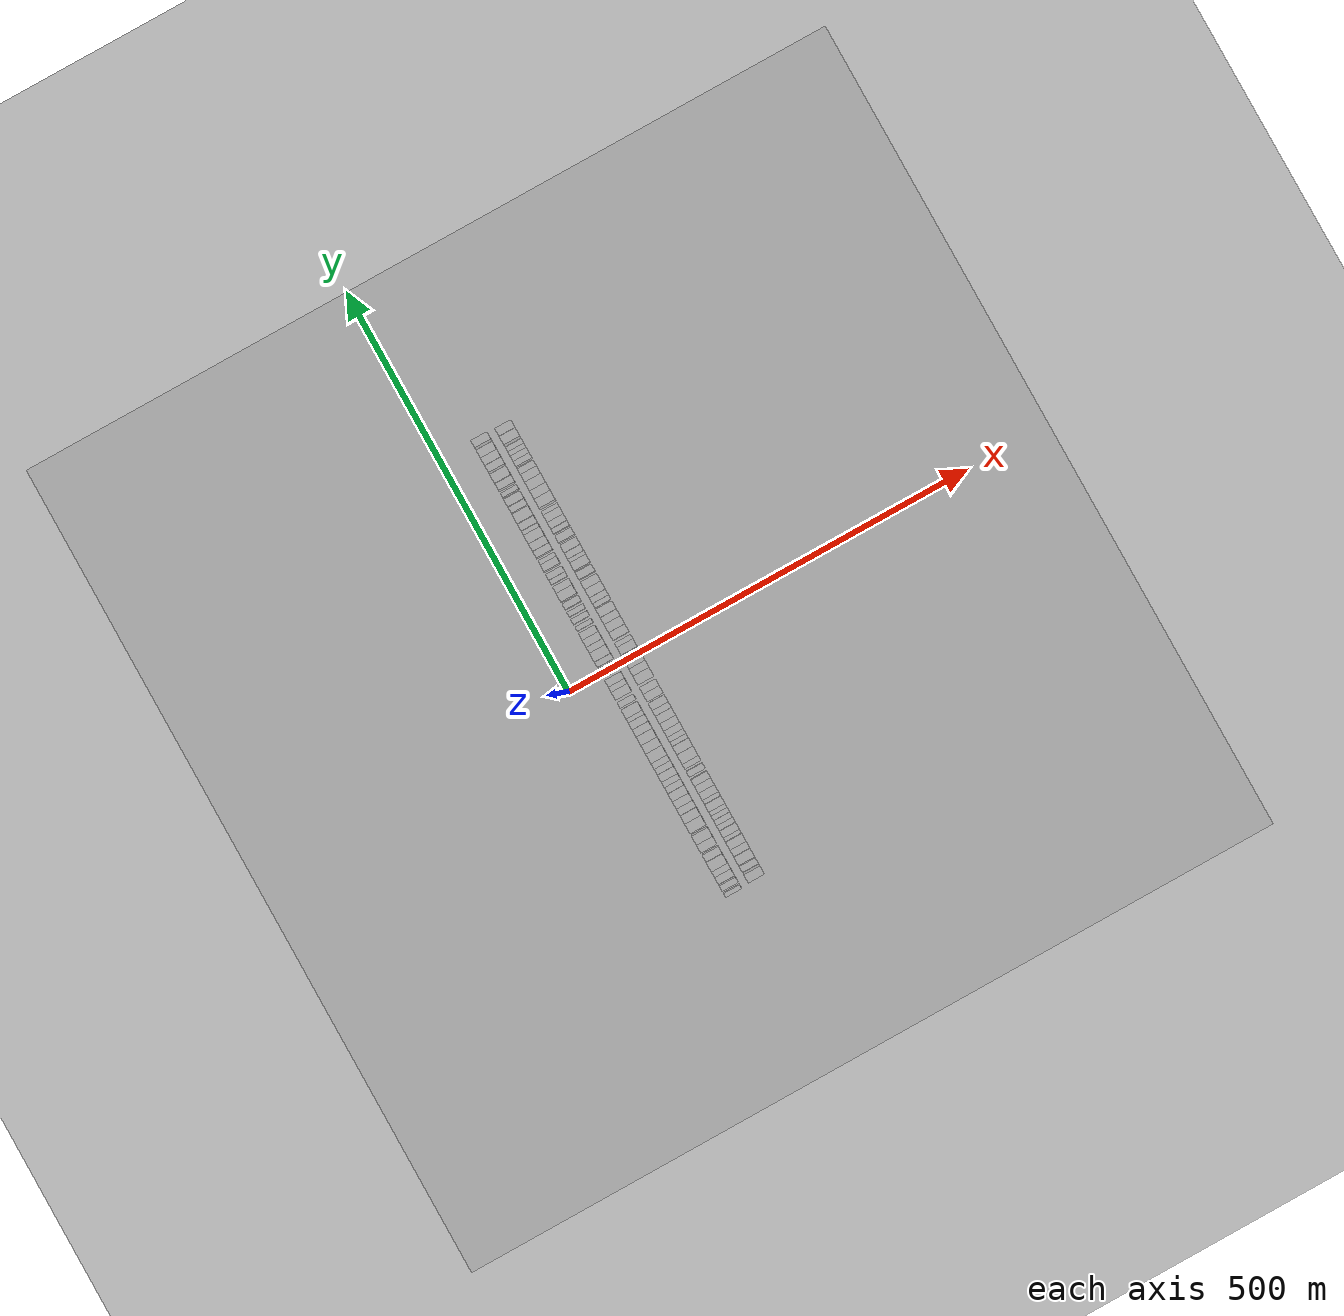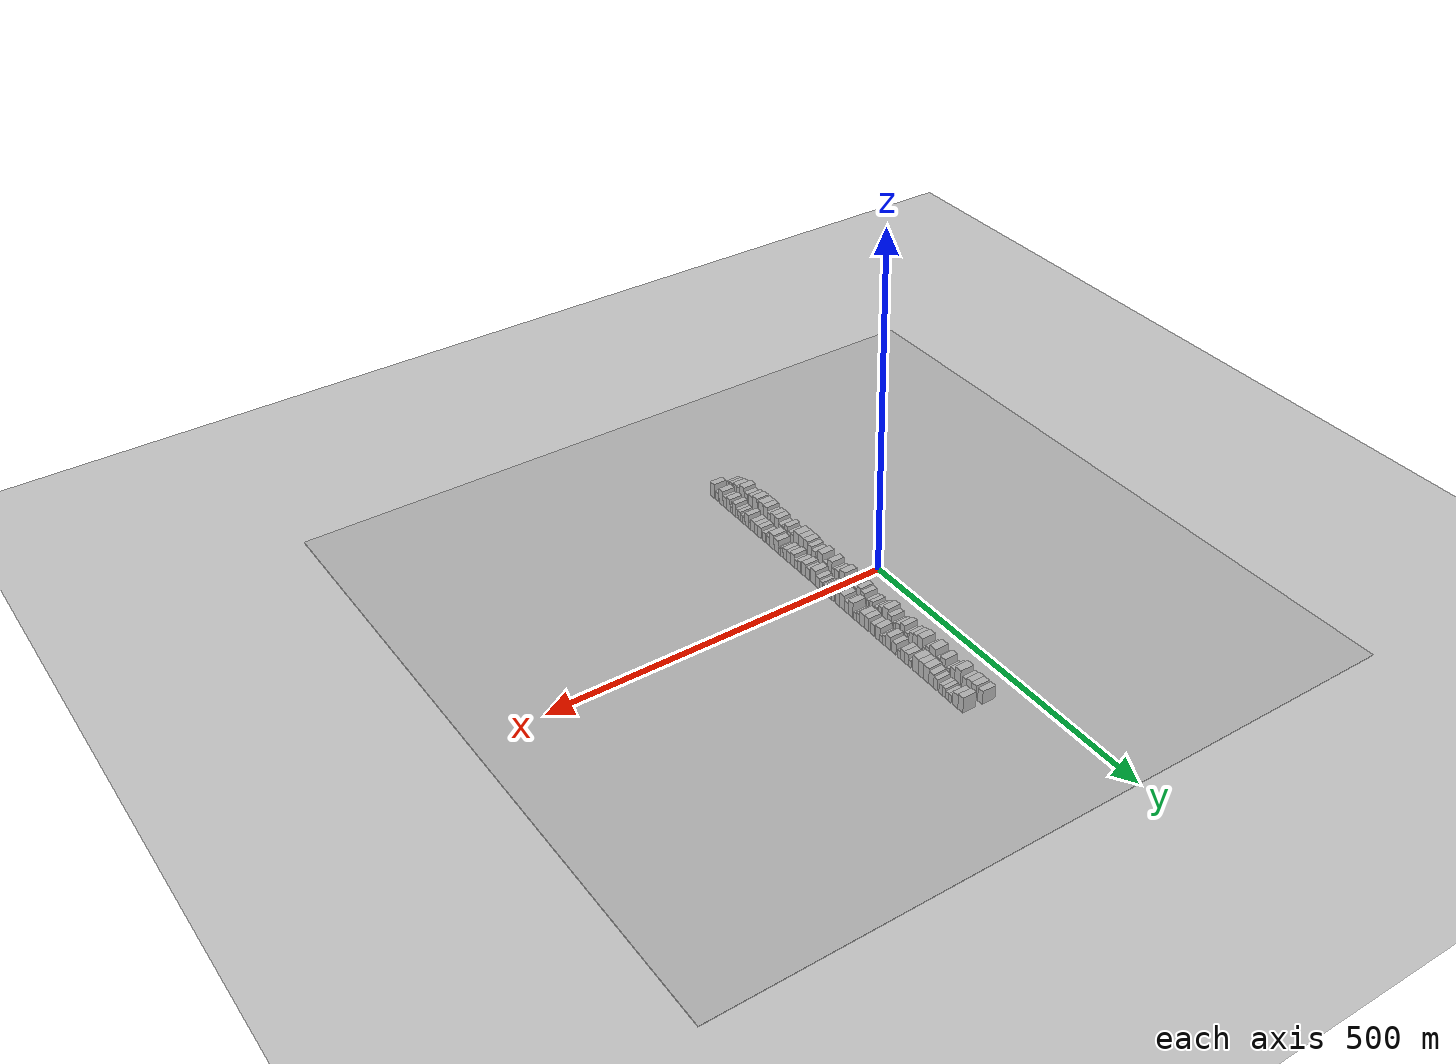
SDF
<?xml version="1.0" encoding="utf-8"?>

<sdf version="1.6">

   <world name="default">

      <gui fullscreen="0">

         <camera name="user_camera">

            <pose>-15 0 4.57585 0 0 0</pose>

            <view_controller>orbit</view_controller>

         </camera>

      </gui>

      <scene>

         <sky>

           <clouds>

             <speed>12</speed>

           </clouds>

         </sky>

         <ambient>0.4 0.4 0.4 1</ambient>

         <background>0.7 0.7 0.7 1</background>

         <shadows>1</shadows>

      </scene>

      <gravity>0 0 -9.8066</gravity>

      <magnetic_field>6e-06 2.3e-05 -4.2e-05</magnetic_field>

      <physics default="0" name="default_physics" type="ode">

         <ode>

            <solver>

               <type>quick</type>

               <iters>10</iters>

               <sor>1.0</sor>

               <use_dynamic_moi_rescaling>0</use_dynamic_moi_rescaling>

            </solver>

            <constraints>

               <cfm>0</cfm>

               <erp>0.2</erp>

               <contact_max_correcting_vel>100</contact_max_correcting_vel>

               <contact_surface_layer>0.001</contact_surface_layer>

            </constraints>

         </ode>

         <max_step_size>0.004</max_step_size>

         <real_time_factor>1</real_time_factor>

         <real_time_update_rate>250</real_time_update_rate>

      </physics>

      <light name="sun" type="directional">

         <cast_shadows>1</cast_shadows>

         <pose>0 0 10 0 0 0</pose>

         <diffuse>0.8 0.8 0.8 1</diffuse>

         <specular>0.2 0.2 0.2 1</specular>

         <attenuation>

            <range>1000</range>

            <constant>0.9</constant>

            <linear>0.01</linear>

            <quadratic>0.001</quadratic>

         </attenuation>

         <direction>-0.5 0.1 -0.9</direction>

      </light>

      <include>

         <name>ground_plane_1</name>

         <uri>model://HANNAS_ground_plane</uri>

         <pose>0 0 0  0 0 0</pose>

      </include>

      <include>

         <name>ground_plane_2</name>

         <uri>model://HANNAS_ground_plane</uri>

         <pose>100 0 0  0 0 0</pose>

      </include>

      <model name="building_1">

         <static>1</static>

         <pose frame="">50.0000 -275.5095 0 0.000000 0.000000 0.000000</pose>

         <link name="link">

            <pose frame="">0 0 6.00 0 0 0</pose>

            <collision name="collision">

               <geometry>

                  <box>

                     <size>20.0000 4.9810 12.0000</size>

                  </box>

               </geometry>

               <max_contacts>10</max_contacts>

               <surface>

                  <contact>

                     <ode/>

                  </contact>

                  <bounce/>

                  <friction>

                     <torsional>

                        <ode/>

                     </torsional>

                     <ode/>

                  </friction>

               </surface>

            </collision>

            <visual name="visual">

               <cast_shadows>0</cast_shadows>

               <geometry>

                  <box>

                     <size>20.0000 4.9810 12.0000</size>

                  </box>

               </geometry>

               <material>

                  <script>

                     <uri>model://HANNAS_wall/materials/scripts</uri>

                     <uri>model://HANNAS_wall/materials/textures</uri>

                     <name>vrc/HANNAS_wall</name>

                  </script>

               </material>

            </visual>

            <self_collide>0</self_collide>

            <enable_wind>0</enable_wind>

            <kinematic>0</kinematic>

         </link>

      </model>

      <model name="building_2">

         <static>1</static>

         <pose frame="">50.0000 -266.6562 0 0.000000 0.000000 0.000000</pose>

         <link name="link">

            <pose frame="">0 0 7.50 0 0 0</pose>

            <collision name="collision">

               <geometry>

                  <box>

                     <size>20.0000 6.7257 15.0000</size>

                  </box>

               </geometry>

               <max_contacts>10</max_contacts>

               <surface>

                  <contact>

                     <ode/>

                  </contact>

                  <bounce/>

                  <friction>

                     <torsional>

                        <ode/>

                     </torsional>

                     <ode/>

                  </friction>

               </surface>

            </collision>

            <visual name="visual">

               <cast_shadows>0</cast_shadows>

               <geometry>

                  <box>

                     <size>20.0000 6.7257 15.0000</size>

                  </box>

               </geometry>

               <material>

                  <script>

                     <uri>model://HANNAS_wall/materials/scripts</uri>

                     <uri>model://HANNAS_wall/materials/textures</uri>

                     <name>vrc/HANNAS_wall</name>

                  </script>

               </material>

            </visual>

            <self_collide>0</self_collide>

            <enable_wind>0</enable_wind>

            <kinematic>0</kinematic>

         </link>

      </model>

      <model name="building_3">

         <static>1</static>

         <pose frame="">50.0000 -256.9734 0 0.000000 0.000000 0.000000</pose>

         <link name="link">

            <pose frame="">0 0 9.00 0 0 0</pose>

            <collision name="collision">

               <geometry>

                  <box>

                     <size>20.0000 8.6398 18.0000</size>

                  </box>

               </geometry>

               <max_contacts>10</max_contacts>

               <surface>

                  <contact>

                     <ode/>

                  </contact>

                  <bounce/>

                  <friction>

                     <torsional>

                        <ode/>

                     </torsional>

                     <ode/>

                  </friction>

               </surface>

            </collision>

            <visual name="visual">

               <cast_shadows>0</cast_shadows>

               <geometry>

                  <box>

                     <size>20.0000 8.6398 18.0000</size>

                  </box>

               </geometry>

               <material>

                  <script>

                     <uri>model://HANNAS_wall/materials/scripts</uri>

                     <uri>model://HANNAS_wall/materials/textures</uri>

                     <name>vrc/HANNAS_wall</name>

                  </script>

               </material>

            </visual>

            <self_collide>0</self_collide>

            <enable_wind>0</enable_wind>

            <kinematic>0</kinematic>

         </link>

      </model>

      <model name="building_4">

         <static>1</static>

         <pose frame="">50.0000 -248.9423 0 0.000000 0.000000 0.000000</pose>

         <link name="link">

            <pose frame="">0 0 9.00 0 0 0</pose>

            <collision name="collision">

               <geometry>

                  <box>

                     <size>20.0000 7.4225 18.0000</size>

                  </box>

               </geometry>

               <max_contacts>10</max_contacts>

               <surface>

                  <contact>

                     <ode/>

                  </contact>

                  <bounce/>

                  <friction>

                     <torsional>

                        <ode/>

                     </torsional>

                     <ode/>

                  </friction>

               </surface>

            </collision>

            <visual name="visual">

               <cast_shadows>0</cast_shadows>

               <geometry>

                  <box>

                     <size>20.0000 7.4225 18.0000</size>

                  </box>

               </geometry>

               <material>

                  <script>

                     <uri>model://HANNAS_wall/materials/scripts</uri>

                     <uri>model://HANNAS_wall/materials/textures</uri>

                     <name>vrc/HANNAS_wall</name>

                  </script>

               </material>

            </visual>

            <self_collide>0</self_collide>

            <enable_wind>0</enable_wind>

            <kinematic>0</kinematic>

         </link>

      </model>

      <model name="building_5">

         <static>1</static>

         <pose frame="">50.0000 -239.3968 0 0.000000 0.000000 0.000000</pose>

         <link name="link">

            <pose frame="">0 0 12.00 0 0 0</pose>

            <collision name="collision">

               <geometry>

                  <box>

                     <size>20.0000 11.6684 24.0000</size>

                  </box>

               </geometry>

               <max_contacts>10</max_contacts>

               <surface>

                  <contact>

                     <ode/>

                  </contact>

                  <bounce/>

                  <friction>

                     <torsional>

                        <ode/>

                     </torsional>

                     <ode/>

                  </friction>

               </surface>

            </collision>

            <visual name="visual">

               <cast_shadows>0</cast_shadows>

               <geometry>

                  <box>

                     <size>20.0000 11.6684 24.0000</size>

                  </box>

               </geometry>

               <material>

                  <script>

                     <uri>model://HANNAS_wall/materials/scripts</uri>

                     <uri>model://HANNAS_wall/materials/textures</uri>

                     <name>vrc/HANNAS_wall</name>

                  </script>

               </material>

            </visual>

            <self_collide>0</self_collide>

            <enable_wind>0</enable_wind>

            <kinematic>0</kinematic>

         </link>

      </model>

      <model name="building_6">

         <static>1</static>

         <pose frame="">50.0000 -229.3155 0 0.000000 0.000000 0.000000</pose>

         <link name="link">

            <pose frame="">0 0 9.00 0 0 0</pose>

            <collision name="collision">

               <geometry>

                  <box>

                     <size>20.0000 8.4943 18.0000</size>

                  </box>

               </geometry>

               <max_contacts>10</max_contacts>

               <surface>

                  <contact>

                     <ode/>

                  </contact>

                  <bounce/>

                  <friction>

                     <torsional>

                        <ode/>

                     </torsional>

                     <ode/>

                  </friction>

               </surface>

            </collision>

            <visual name="visual">

               <cast_shadows>0</cast_shadows>

               <geometry>

                  <box>

                     <size>20.0000 8.4943 18.0000</size>

                  </box>

               </geometry>

               <material>

                  <script>

                     <uri>model://HANNAS_wall/materials/scripts</uri>

                     <uri>model://HANNAS_wall/materials/textures</uri>

                     <name>vrc/HANNAS_wall</name>

                  </script>

               </material>

            </visual>

            <self_collide>0</self_collide>

            <enable_wind>0</enable_wind>

            <kinematic>0</kinematic>

         </link>

      </model>

      <model name="building_7">

         <static>1</static>

         <pose frame="">50.0000 -217.0728 0 0.000000 0.000000 0.000000</pose>

         <link name="link">

            <pose frame="">0 0 10.50 0 0 0</pose>

            <collision name="collision">

               <geometry>

                  <box>

                     <size>20.0000 9.9910 21.0000</size>

                  </box>

               </geometry>

               <max_contacts>10</max_contacts>

               <surface>

                  <contact>

                     <ode/>

                  </contact>

                  <bounce/>

                  <friction>

                     <torsional>

                        <ode/>

                     </torsional>

                     <ode/>

                  </friction>

               </surface>

            </collision>

            <visual name="visual">

               <cast_shadows>0</cast_shadows>

               <geometry>

                  <box>

                     <size>20.0000 9.9910 21.0000</size>

                  </box>

               </geometry>

               <material>

                  <script>

                     <uri>model://HANNAS_wall/materials/scripts</uri>

                     <uri>model://HANNAS_wall/materials/textures</uri>

                     <name>vrc/HANNAS_wall</name>

                  </script>

               </material>

            </visual>

            <self_collide>0</self_collide>

            <enable_wind>0</enable_wind>

            <kinematic>0</kinematic>

         </link>

      </model>

      <model name="building_8">

         <static>1</static>

         <pose frame="">50.0000 -206.5521 0 0.000000 0.000000 0.000000</pose>

         <link name="link">

            <pose frame="">0 0 12.00 0 0 0</pose>

            <collision name="collision">

               <geometry>

                  <box>

                     <size>20.0000 11.0504 24.0000</size>

                  </box>

               </geometry>

               <max_contacts>10</max_contacts>

               <surface>

                  <contact>

                     <ode/>

                  </contact>

                  <bounce/>

                  <friction>

                     <torsional>

                        <ode/>

                     </torsional>

                     <ode/>

                  </friction>

               </surface>

            </collision>

            <visual name="visual">

               <cast_shadows>0</cast_shadows>

               <geometry>

                  <box>

                     <size>20.0000 11.0504 24.0000</size>

                  </box>

               </geometry>

               <material>

                  <script>

                     <uri>model://HANNAS_wall/materials/scripts</uri>

                     <uri>model://HANNAS_wall/materials/textures</uri>

                     <name>vrc/HANNAS_wall</name>

                  </script>

               </material>

            </visual>

            <self_collide>0</self_collide>

            <enable_wind>0</enable_wind>

            <kinematic>0</kinematic>

         </link>

      </model>

      <model name="building_9">

         <static>1</static>

         <pose frame="">50.0000 -192.0702 0 0.000000 0.000000 0.000000</pose>

         <link name="link">

            <pose frame="">0 0 12.00 0 0 0</pose>

            <collision name="collision">

               <geometry>

                  <box>

                     <size>20.0000 11.9134 24.0000</size>

                  </box>

               </geometry>

               <max_contacts>10</max_contacts>

               <surface>

                  <contact>

                     <ode/>

                  </contact>

                  <bounce/>

                  <friction>

                     <torsional>

                        <ode/>

                     </torsional>

                     <ode/>

                  </friction>

               </surface>

            </collision>

            <visual name="visual">

               <cast_shadows>0</cast_shadows>

               <geometry>

                  <box>

                     <size>20.0000 11.9134 24.0000</size>

                  </box>

               </geometry>

               <material>

                  <script>

                     <uri>model://HANNAS_wall/materials/scripts</uri>

                     <uri>model://HANNAS_wall/materials/textures</uri>

                     <name>vrc/HANNAS_wall</name>

                  </script>

               </material>

            </visual>

            <self_collide>0</self_collide>

            <enable_wind>0</enable_wind>

            <kinematic>0</kinematic>

         </link>

      </model>

      <model name="building_10">

         <static>1</static>

         <pose frame="">50.0000 -181.1173 0 0.000000 0.000000 0.000000</pose>

         <link name="link">

            <pose frame="">0 0 12.00 0 0 0</pose>

            <collision name="collision">

               <geometry>

                  <box>

                     <size>20.0000 9.9924 24.0000</size>

                  </box>

               </geometry>

               <max_contacts>10</max_contacts>

               <surface>

                  <contact>

                     <ode/>

                  </contact>

                  <bounce/>

                  <friction>

                     <torsional>

                        <ode/>

                     </torsional>

                     <ode/>

                  </friction>

               </surface>

            </collision>

            <visual name="visual">

               <cast_shadows>0</cast_shadows>

               <geometry>

                  <box>

                     <size>20.0000 9.9924 24.0000</size>

                  </box>

               </geometry>

               <material>

                  <script>

                     <uri>model://HANNAS_wall/materials/scripts</uri>

                     <uri>model://HANNAS_wall/materials/textures</uri>

                     <name>vrc/HANNAS_wall</name>

                  </script>

               </material>

            </visual>

            <self_collide>0</self_collide>

            <enable_wind>0</enable_wind>

            <kinematic>0</kinematic>

         </link>

      </model>

      <model name="building_11">

         <static>1</static>

         <pose frame="">50.0000 -171.9731 0 0.000000 0.000000 0.000000</pose>

         <link name="link">

            <pose frame="">0 0 9.00 0 0 0</pose>

            <collision name="collision">

               <geometry>

                  <box>

                     <size>20.0000 8.2960 18.0000</size>

                  </box>

               </geometry>

               <max_contacts>10</max_contacts>

               <surface>

                  <contact>

                     <ode/>

                  </contact>

                  <bounce/>

                  <friction>

                     <torsional>

                        <ode/>

                     </torsional>

                     <ode/>

                  </friction>

               </surface>

            </collision>

            <visual name="visual">

               <cast_shadows>0</cast_shadows>

               <geometry>

                  <box>

                     <size>20.0000 8.2960 18.0000</size>

                  </box>

               </geometry>

               <material>

                  <script>

                     <uri>model://HANNAS_wall/materials/scripts</uri>

                     <uri>model://HANNAS_wall/materials/textures</uri>

                     <name>vrc/HANNAS_wall</name>

                  </script>

               </material>

            </visual>

            <self_collide>0</self_collide>

            <enable_wind>0</enable_wind>

            <kinematic>0</kinematic>

         </link>

      </model>

      <model name="building_12">

         <static>1</static>

         <pose frame="">50.0000 -163.3178 0 0.000000 0.000000 0.000000</pose>

         <link name="link">

            <pose frame="">0 0 10.50 0 0 0</pose>

            <collision name="collision">

               <geometry>

                  <box>

                     <size>20.0000 9.0146 21.0000</size>

                  </box>

               </geometry>

               <max_contacts>10</max_contacts>

               <surface>

                  <contact>

                     <ode/>

                  </contact>

                  <bounce/>

                  <friction>

                     <torsional>

                        <ode/>

                     </torsional>

                     <ode/>

                  </friction>

               </surface>

            </collision>

            <visual name="visual">

               <cast_shadows>0</cast_shadows>

               <geometry>

                  <box>

                     <size>20.0000 9.0146 21.0000</size>

                  </box>

               </geometry>

               <material>

                  <script>

                     <uri>model://HANNAS_wall/materials/scripts</uri>

                     <uri>model://HANNAS_wall/materials/textures</uri>

                     <name>vrc/HANNAS_wall</name>

                  </script>

               </material>

            </visual>

            <self_collide>0</self_collide>

            <enable_wind>0</enable_wind>

            <kinematic>0</kinematic>

         </link>

      </model>

      <model name="building_13">

         <static>1</static>

         <pose frame="">50.0000 -153.9079 0 0.000000 0.000000 0.000000</pose>

         <link name="link">

            <pose frame="">0 0 10.50 0 0 0</pose>

            <collision name="collision">

               <geometry>

                  <box>

                     <size>20.0000 9.8053 21.0000</size>

                  </box>

               </geometry>

               <max_contacts>10</max_contacts>

               <surface>

                  <contact>

                     <ode/>

                  </contact>

                  <bounce/>

                  <friction>

                     <torsional>

                        <ode/>

                     </torsional>

                     <ode/>

                  </friction>

               </surface>

            </collision>

            <visual name="visual">

               <cast_shadows>0</cast_shadows>

               <geometry>

                  <box>

                     <size>20.0000 9.8053 21.0000</size>

                  </box>

               </geometry>

               <material>

                  <script>

                     <uri>model://HANNAS_wall/materials/scripts</uri>

                     <uri>model://HANNAS_wall/materials/textures</uri>

                     <name>vrc/HANNAS_wall</name>

                  </script>

               </material>

            </visual>

            <self_collide>0</self_collide>

            <enable_wind>0</enable_wind>

            <kinematic>0</kinematic>

         </link>

      </model>

      <model name="building_14">

         <static>1</static>

         <pose frame="">50.0000 -145.3055 0 0.000000 0.000000 0.000000</pose>

         <link name="link">

            <pose frame="">0 0 7.50 0 0 0</pose>

            <collision name="collision">

               <geometry>

                  <box>

                     <size>20.0000 7.3994 15.0000</size>

                  </box>

               </geometry>

               <max_contacts>10</max_contacts>

               <surface>

                  <contact>

                     <ode/>

                  </contact>

                  <bounce/>

                  <friction>

                     <torsional>

                        <ode/>

                     </torsional>

                     <ode/>

                  </friction>

               </surface>

            </collision>

            <visual name="visual">

               <cast_shadows>0</cast_shadows>

               <geometry>

                  <box>

                     <size>20.0000 7.3994 15.0000</size>

                  </box>

               </geometry>

               <material>

                  <script>

                     <uri>model://HANNAS_wall/materials/scripts</uri>

                     <uri>model://HANNAS_wall/materials/textures</uri>

                     <name>vrc/HANNAS_wall</name>

                  </script>

               </material>

            </visual>

            <self_collide>0</self_collide>

            <enable_wind>0</enable_wind>

            <kinematic>0</kinematic>

         </link>

      </model>

      <model name="building_15">

         <static>1</static>

         <pose frame="">50.0000 -138.1473 0 0.000000 0.000000 0.000000</pose>

         <link name="link">

            <pose frame="">0 0 7.50 0 0 0</pose>

            <collision name="collision">

               <geometry>

                  <box>

                     <size>20.0000 6.9170 15.0000</size>

                  </box>

               </geometry>

               <max_contacts>10</max_contacts>

               <surface>

                  <contact>

                     <ode/>

                  </contact>

                  <bounce/>

                  <friction>

                     <torsional>

                        <ode/>

                     </torsional>

                     <ode/>

                  </friction>

               </surface>

            </collision>

            <visual name="visual">

               <cast_shadows>0</cast_shadows>

               <geometry>

                  <box>

                     <size>20.0000 6.9170 15.0000</size>

                  </box>

               </geometry>

               <material>

                  <script>

                     <uri>model://HANNAS_wall/materials/scripts</uri>

                     <uri>model://HANNAS_wall/materials/textures</uri>

                     <name>vrc/HANNAS_wall</name>

                  </script>

               </material>

            </visual>

            <self_collide>0</self_collide>

            <enable_wind>0</enable_wind>

            <kinematic>0</kinematic>

         </link>

      </model>

      <model name="building_16">

         <static>1</static>

         <pose frame="">50.0000 -130.2422 0 0.000000 0.000000 0.000000</pose>

         <link name="link">

            <pose frame="">0 0 10.50 0 0 0</pose>

            <collision name="collision">

               <geometry>

                  <box>

                     <size>20.0000 8.8931 21.0000</size>

                  </box>

               </geometry>

               <max_contacts>10</max_contacts>

               <surface>

                  <contact>

                     <ode/>

                  </contact>

                  <bounce/>

                  <friction>

                     <torsional>

                        <ode/>

                     </torsional>

                     <ode/>

                  </friction>

               </surface>

            </collision>

            <visual name="visual">

               <cast_shadows>0</cast_shadows>

               <geometry>

                  <box>

                     <size>20.0000 8.8931 21.0000</size>

                  </box>

               </geometry>

               <material>

                  <script>

                     <uri>model://HANNAS_wall/materials/scripts</uri>

                     <uri>model://HANNAS_wall/materials/textures</uri>

                     <name>vrc/HANNAS_wall</name>

                  </script>

               </material>

            </visual>

            <self_collide>0</self_collide>

            <enable_wind>0</enable_wind>

            <kinematic>0</kinematic>

         </link>

      </model>

      <model name="building_17">

         <static>1</static>

         <pose frame="">50.0000 -122.2671 0 0.000000 0.000000 0.000000</pose>

         <link name="link">

            <pose frame="">0 0 7.50 0 0 0</pose>

            <collision name="collision">

               <geometry>

                  <box>

                     <size>20.0000 7.0571 15.0000</size>

                  </box>

               </geometry>

               <max_contacts>10</max_contacts>

               <surface>

                  <contact>

                     <ode/>

                  </contact>

                  <bounce/>

                  <friction>

                     <torsional>

                        <ode/>

                     </torsional>

                     <ode/>

                  </friction>

               </surface>

            </collision>

            <visual name="visual">

               <cast_shadows>0</cast_shadows>

               <geometry>

                  <box>

                     <size>20.0000 7.0571 15.0000</size>

                  </box>

               </geometry>

               <material>

                  <script>

                     <uri>model://HANNAS_wall/materials/scripts</uri>

                     <uri>model://HANNAS_wall/materials/textures</uri>

                     <name>vrc/HANNAS_wall</name>

                  </script>

               </material>

            </visual>

            <self_collide>0</self_collide>

            <enable_wind>0</enable_wind>

            <kinematic>0</kinematic>

         </link>

      </model>

      <model name="building_18">

         <static>1</static>

         <pose frame="">50.0000 -115.1416 0 0.000000 0.000000 0.000000</pose>

         <link name="link">

            <pose frame="">0 0 7.50 0 0 0</pose>

            <collision name="collision">

               <geometry>

                  <box>

                     <size>20.0000 7.1939 15.0000</size>

                  </box>

               </geometry>

               <max_contacts>10</max_contacts>

               <surface>

                  <contact>

                     <ode/>

                  </contact>

                  <bounce/>

                  <friction>

                     <torsional>

                        <ode/>

                     </torsional>

                     <ode/>

                  </friction>

               </surface>

            </collision>

            <visual name="visual">

               <cast_shadows>0</cast_shadows>

               <geometry>

                  <box>

                     <size>20.0000 7.1939 15.0000</size>

                  </box>

               </geometry>

               <material>

                  <script>

                     <uri>model://HANNAS_wall/materials/scripts</uri>

                     <uri>model://HANNAS_wall/materials/textures</uri>

                     <name>vrc/HANNAS_wall</name>

                  </script>

               </material>

            </visual>

            <self_collide>0</self_collide>

            <enable_wind>0</enable_wind>

            <kinematic>0</kinematic>

         </link>

      </model>

      <model name="building_19">

         <static>1</static>

         <pose frame="">50.0000 -105.5763 0 0.000000 0.000000 0.000000</pose>

         <link name="link">

            <pose frame="">0 0 12.00 0 0 0</pose>

            <collision name="collision">

               <geometry>

                  <box>

                     <size>20.0000 11.9367 24.0000</size>

                  </box>

               </geometry>

               <max_contacts>10</max_contacts>

               <surface>

                  <contact>

                     <ode/>

                  </contact>

                  <bounce/>

                  <friction>

                     <torsional>

                        <ode/>

                     </torsional>

                     <ode/>

                  </friction>

               </surface>

            </collision>

            <visual name="visual">

               <cast_shadows>0</cast_shadows>

               <geometry>

                  <box>

                     <size>20.0000 11.9367 24.0000</size>

                  </box>

               </geometry>

               <material>

                  <script>

                     <uri>model://HANNAS_wall/materials/scripts</uri>

                     <uri>model://HANNAS_wall/materials/textures</uri>

                     <name>vrc/HANNAS_wall</name>

                  </script>

               </material>

            </visual>

            <self_collide>0</self_collide>

            <enable_wind>0</enable_wind>

            <kinematic>0</kinematic>

         </link>

      </model>

      <model name="building_20">

         <static>1</static>

         <pose frame="">50.0000 -94.4235 0 0.000000 0.000000 0.000000</pose>

         <link name="link">

            <pose frame="">0 0 12.00 0 0 0</pose>

            <collision name="collision">

               <geometry>

                  <box>

                     <size>20.0000 10.3688 24.0000</size>

                  </box>

               </geometry>

               <max_contacts>10</max_contacts>

               <surface>

                  <contact>

                     <ode/>

                  </contact>

                  <bounce/>

                  <friction>

                     <torsional>

                        <ode/>

                     </torsional>

                     <ode/>

                  </friction>

               </surface>

            </collision>

            <visual name="visual">

               <cast_shadows>0</cast_shadows>

               <geometry>

                  <box>

                     <size>20.0000 10.3688 24.0000</size>

                  </box>

               </geometry>

               <material>

                  <script>

                     <uri>model://HANNAS_wall/materials/scripts</uri>

                     <uri>model://HANNAS_wall/materials/textures</uri>

                     <name>vrc/HANNAS_wall</name>

                  </script>

               </material>

            </visual>

            <self_collide>0</self_collide>

            <enable_wind>0</enable_wind>

            <kinematic>0</kinematic>

         </link>

      </model>

      <model name="building_21">

         <static>1</static>

         <pose frame="">50.0000 -83.8943 0 0.000000 0.000000 0.000000</pose>

         <link name="link">

            <pose frame="">0 0 12.00 0 0 0</pose>

            <collision name="collision">

               <geometry>

                  <box>

                     <size>20.0000 10.6895 24.0000</size>

                  </box>

               </geometry>

               <max_contacts>10</max_contacts>

               <surface>

                  <contact>

                     <ode/>

                  </contact>

                  <bounce/>

                  <friction>

                     <torsional>

                        <ode/>

                     </torsional>

                     <ode/>

                  </friction>

               </surface>

            </collision>

            <visual name="visual">

               <cast_shadows>0</cast_shadows>

               <geometry>

                  <box>

                     <size>20.0000 10.6895 24.0000</size>

                  </box>

               </geometry>

               <material>

                  <script>

                     <uri>model://HANNAS_wall/materials/scripts</uri>

                     <uri>model://HANNAS_wall/materials/textures</uri>

                     <name>vrc/HANNAS_wall</name>

                  </script>

               </material>

            </visual>

            <self_collide>0</self_collide>

            <enable_wind>0</enable_wind>

            <kinematic>0</kinematic>

         </link>

      </model>

      <model name="building_22">

         <static>1</static>

         <pose frame="">50.0000 -74.1947 0 0.000000 0.000000 0.000000</pose>

         <link name="link">

            <pose frame="">0 0 10.50 0 0 0</pose>

            <collision name="collision">

               <geometry>

                  <box>

                     <size>20.0000 8.7096 21.0000</size>

                  </box>

               </geometry>

               <max_contacts>10</max_contacts>

               <surface>

                  <contact>

                     <ode/>

                  </contact>

                  <bounce/>

                  <friction>

                     <torsional>

                        <ode/>

                     </torsional>

                     <ode/>

                  </friction>

               </surface>

            </collision>

            <visual name="visual">

               <cast_shadows>0</cast_shadows>

               <geometry>

                  <box>

                     <size>20.0000 8.7096 21.0000</size>

                  </box>

               </geometry>

               <material>

                  <script>

                     <uri>model://HANNAS_wall/materials/scripts</uri>

                     <uri>model://HANNAS_wall/materials/textures</uri>

                     <name>vrc/HANNAS_wall</name>

                  </script>

               </material>

            </visual>

            <self_collide>0</self_collide>

            <enable_wind>0</enable_wind>

            <kinematic>0</kinematic>

         </link>

      </model>

      <model name="building_23">

         <static>1</static>

         <pose frame="">50.0000 -65.5547 0 0.000000 0.000000 0.000000</pose>

         <link name="link">

            <pose frame="">0 0 9.00 0 0 0</pose>

            <collision name="collision">

               <geometry>

                  <box>

                     <size>20.0000 8.5704 18.0000</size>

                  </box>

               </geometry>

               <max_contacts>10</max_contacts>

               <surface>

                  <contact>

                     <ode/>

                  </contact>

                  <bounce/>

                  <friction>

                     <torsional>

                        <ode/>

                     </torsional>

                     <ode/>

                  </friction>

               </surface>

            </collision>

            <visual name="visual">

               <cast_shadows>0</cast_shadows>

               <geometry>

                  <box>

                     <size>20.0000 8.5704 18.0000</size>

                  </box>

               </geometry>

               <material>

                  <script>

                     <uri>model://HANNAS_wall/materials/scripts</uri>

                     <uri>model://HANNAS_wall/materials/textures</uri>

                     <name>vrc/HANNAS_wall</name>

                  </script>

               </material>

            </visual>

            <self_collide>0</self_collide>

            <enable_wind>0</enable_wind>

            <kinematic>0</kinematic>

         </link>

      </model>

      <model name="building_24">

         <static>1</static>

         <pose frame="">50.0000 -58.7450 0 0.000000 0.000000 0.000000</pose>

         <link name="link">

            <pose frame="">0 0 6.00 0 0 0</pose>

            <collision name="collision">

               <geometry>

                  <box>

                     <size>20.0000 5.0491 12.0000</size>

                  </box>

               </geometry>

               <max_contacts>10</max_contacts>

               <surface>

                  <contact>

                     <ode/>

                  </contact>

                  <bounce/>

                  <friction>

                     <torsional>

                        <ode/>

                     </torsional>

                     <ode/>

                  </friction>

               </surface>

            </collision>

            <visual name="visual">

               <cast_shadows>0</cast_shadows>

               <geometry>

                  <box>

                     <size>20.0000 5.0491 12.0000</size>

                  </box>

               </geometry>

               <material>

                  <script>

                     <uri>model://HANNAS_wall/materials/scripts</uri>

                     <uri>model://HANNAS_wall/materials/textures</uri>

                     <name>vrc/HANNAS_wall</name>

                  </script>

               </material>

            </visual>

            <self_collide>0</self_collide>

            <enable_wind>0</enable_wind>

            <kinematic>0</kinematic>

         </link>

      </model>

      <model name="building_25">

         <static>1</static>

         <pose frame="">50.0000 -50.6894 0 0.000000 0.000000 0.000000</pose>

         <link name="link">

            <pose frame="">0 0 12.00 0 0 0</pose>

            <collision name="collision">

               <geometry>

                  <box>

                     <size>20.0000 11.0620 24.0000</size>

                  </box>

               </geometry>

               <max_contacts>10</max_contacts>

               <surface>

                  <contact>

                     <ode/>

                  </contact>

                  <bounce/>

                  <friction>

                     <torsional>

                        <ode/>

                     </torsional>

                     <ode/>

                  </friction>

               </surface>

            </collision>

            <visual name="visual">

               <cast_shadows>0</cast_shadows>

               <geometry>

                  <box>

                     <size>20.0000 11.0620 24.0000</size>

                  </box>

               </geometry>

               <material>

                  <script>

                     <uri>model://HANNAS_wall/materials/scripts</uri>

                     <uri>model://HANNAS_wall/materials/textures</uri>

                     <name>vrc/HANNAS_wall</name>

                  </script>

               </material>

            </visual>

            <self_collide>0</self_collide>

            <enable_wind>0</enable_wind>

            <kinematic>0</kinematic>

         </link>

      </model>

      <model name="building_26">

         <static>1</static>

         <pose frame="">50.0000 -39.6326 0 0.000000 0.000000 0.000000</pose>

         <link name="link">

            <pose frame="">0 0 7.50 0 0 0</pose>

            <collision name="collision">

               <geometry>

                  <box>

                     <size>20.0000 7.0516 15.0000</size>

                  </box>

               </geometry>

               <max_contacts>10</max_contacts>

               <surface>

                  <contact>

                     <ode/>

                  </contact>

                  <bounce/>

                  <friction>

                     <torsional>

                        <ode/>

                     </torsional>

                     <ode/>

                  </friction>

               </surface>

            </collision>

            <visual name="visual">

               <cast_shadows>0</cast_shadows>

               <geometry>

                  <box>

                     <size>20.0000 7.0516 15.0000</size>

                  </box>

               </geometry>

               <material>

                  <script>

                     <uri>model://HANNAS_wall/materials/scripts</uri>

                     <uri>model://HANNAS_wall/materials/textures</uri>

                     <name>vrc/HANNAS_wall</name>

                  </script>

               </material>

            </visual>

            <self_collide>0</self_collide>

            <enable_wind>0</enable_wind>

            <kinematic>0</kinematic>

         </link>

      </model>

      <model name="building_27">

         <static>1</static>

         <pose frame="">50.0000 -28.1951 0 0.000000 0.000000 0.000000</pose>

         <link name="link">

            <pose frame="">0 0 12.00 0 0 0</pose>

            <collision name="collision">

               <geometry>

                  <box>

                     <size>20.0000 9.8236 24.0000</size>

                  </box>

               </geometry>

               <max_contacts>10</max_contacts>

               <surface>

                  <contact>

                     <ode/>

                  </contact>

                  <bounce/>

                  <friction>

                     <torsional>

                        <ode/>

                     </torsional>

                     <ode/>

                  </friction>

               </surface>

            </collision>

            <visual name="visual">

               <cast_shadows>0</cast_shadows>

               <geometry>

                  <box>

                     <size>20.0000 9.8236 24.0000</size>

                  </box>

               </geometry>

               <material>

                  <script>

                     <uri>model://HANNAS_wall/materials/scripts</uri>

                     <uri>model://HANNAS_wall/materials/textures</uri>

                     <name>vrc/HANNAS_wall</name>

                  </script>

               </material>

            </visual>

            <self_collide>0</self_collide>

            <enable_wind>0</enable_wind>

            <kinematic>0</kinematic>

         </link>

      </model>

      <model name="building_28">

         <static>1</static>

         <pose frame="">50.0000 -20.1003 0 0.000000 0.000000 0.000000</pose>

         <link name="link">

            <pose frame="">0 0 7.50 0 0 0</pose>

            <collision name="collision">

               <geometry>

                  <box>

                     <size>20.0000 6.3659 15.0000</size>

                  </box>

               </geometry>

               <max_contacts>10</max_contacts>

               <surface>

                  <contact>

                     <ode/>

                  </contact>

                  <bounce/>

                  <friction>

                     <torsional>

                        <ode/>

                     </torsional>

                     <ode/>

                  </friction>

               </surface>

            </collision>

            <visual name="visual">

               <cast_shadows>0</cast_shadows>

               <geometry>

                  <box>

                     <size>20.0000 6.3659 15.0000</size>

                  </box>

               </geometry>

               <material>

                  <script>

                     <uri>model://HANNAS_wall/materials/scripts</uri>

                     <uri>model://HANNAS_wall/materials/textures</uri>

                     <name>vrc/HANNAS_wall</name>

                  </script>

               </material>

            </visual>

            <self_collide>0</self_collide>

            <enable_wind>0</enable_wind>

            <kinematic>0</kinematic>

         </link>

      </model>

      <model name="building_29">

         <static>1</static>

         <pose frame="">50.0000 -12.6781 0 0.000000 0.000000 0.000000</pose>

         <link name="link">

            <pose frame="">0 0 9.00 0 0 0</pose>

            <collision name="collision">

               <geometry>

                  <box>

                     <size>20.0000 8.4785 18.0000</size>

                  </box>

               </geometry>

               <max_contacts>10</max_contacts>

               <surface>

                  <contact>

                     <ode/>

                  </contact>

                  <bounce/>

                  <friction>

                     <torsional>

                        <ode/>

                     </torsional>

                     <ode/>

                  </friction>

               </surface>

            </collision>

            <visual name="visual">

               <cast_shadows>0</cast_shadows>

               <geometry>

                  <box>

                     <size>20.0000 8.4785 18.0000</size>

                  </box>

               </geometry>

               <material>

                  <script>

                     <uri>model://HANNAS_wall/materials/scripts</uri>

                     <uri>model://HANNAS_wall/materials/textures</uri>

                     <name>vrc/HANNAS_wall</name>

                  </script>

               </material>

            </visual>

            <self_collide>0</self_collide>

            <enable_wind>0</enable_wind>

            <kinematic>0</kinematic>

         </link>

      </model>

      <model name="building_30">

         <static>1</static>

         <pose frame="">50.0000 0.0246 0 0.000000 0.000000 0.000000</pose>

         <link name="link">

            <pose frame="">0 0 12.00 0 0 0</pose>

            <collision name="collision">

               <geometry>

                  <box>

                     <size>20.0000 10.9269 24.0000</size>

                  </box>

               </geometry>

               <max_contacts>10</max_contacts>

               <surface>

                  <contact>

                     <ode/>

                  </contact>

                  <bounce/>

                  <friction>

                     <torsional>

                        <ode/>

                     </torsional>

                     <ode/>

                  </friction>

               </surface>

            </collision>

            <visual name="visual">

               <cast_shadows>0</cast_shadows>

               <geometry>

                  <box>

                     <size>20.0000 10.9269 24.0000</size>

                  </box>

               </geometry>

               <material>

                  <script>

                     <uri>model://HANNAS_wall/materials/scripts</uri>

                     <uri>model://HANNAS_wall/materials/textures</uri>

                     <name>vrc/HANNAS_wall</name>

                  </script>

               </material>

            </visual>

            <self_collide>0</self_collide>

            <enable_wind>0</enable_wind>

            <kinematic>0</kinematic>

         </link>

      </model>

      <model name="building_31">

         <static>1</static>

         <pose frame="">50.0000 10.7795 0 0.000000 0.000000 0.000000</pose>

         <link name="link">

            <pose frame="">0 0 7.50 0 0 0</pose>

            <collision name="collision">

               <geometry>

                  <box>

                     <size>20.0000 6.5830 15.0000</size>

                  </box>

               </geometry>

               <max_contacts>10</max_contacts>

               <surface>

                  <contact>

                     <ode/>

                  </contact>

                  <bounce/>

                  <friction>

                     <torsional>

                        <ode/>

                     </torsional>

                     <ode/>

                  </friction>

               </surface>

            </collision>

            <visual name="visual">

               <cast_shadows>0</cast_shadows>

               <geometry>

                  <box>

                     <size>20.0000 6.5830 15.0000</size>

                  </box>

               </geometry>

               <material>

                  <script>

                     <uri>model://HANNAS_wall/materials/scripts</uri>

                     <uri>model://HANNAS_wall/materials/textures</uri>

                     <name>vrc/HANNAS_wall</name>

                  </script>

               </material>

            </visual>

            <self_collide>0</self_collide>

            <enable_wind>0</enable_wind>

            <kinematic>0</kinematic>

         </link>

      </model>

      <model name="building_32">

         <static>1</static>

         <pose frame="">50.0000 19.5707 0 0.000000 0.000000 0.000000</pose>

         <link name="link">

            <pose frame="">0 0 12.00 0 0 0</pose>

            <collision name="collision">

               <geometry>

                  <box>

                     <size>20.0000 10.9994 24.0000</size>

                  </box>

               </geometry>

               <max_contacts>10</max_contacts>

               <surface>

                  <contact>

                     <ode/>

                  </contact>

                  <bounce/>

                  <friction>

                     <torsional>

                        <ode/>

                     </torsional>

                     <ode/>

                  </friction>

               </surface>

            </collision>

            <visual name="visual">

               <cast_shadows>0</cast_shadows>

               <geometry>

                  <box>

                     <size>20.0000 10.9994 24.0000</size>

                  </box>

               </geometry>

               <material>

                  <script>

                     <uri>model://HANNAS_wall/materials/scripts</uri>

                     <uri>model://HANNAS_wall/materials/textures</uri>

                     <name>vrc/HANNAS_wall</name>

                  </script>

               </material>

            </visual>

            <self_collide>0</self_collide>

            <enable_wind>0</enable_wind>

            <kinematic>0</kinematic>

         </link>

      </model>

      <model name="building_33">

         <static>1</static>

         <pose frame="">50.0000 28.7614 0 0.000000 0.000000 0.000000</pose>

         <link name="link">

            <pose frame="">0 0 7.50 0 0 0</pose>

            <collision name="collision">

               <geometry>

                  <box>

                     <size>20.0000 7.3819 15.0000</size>

                  </box>

               </geometry>

               <max_contacts>10</max_contacts>

               <surface>

                  <contact>

                     <ode/>

                  </contact>

                  <bounce/>

                  <friction>

                     <torsional>

                        <ode/>

                     </torsional>

                     <ode/>

                  </friction>

               </surface>

            </collision>

            <visual name="visual">

               <cast_shadows>0</cast_shadows>

               <geometry>

                  <box>

                     <size>20.0000 7.3819 15.0000</size>

                  </box>

               </geometry>

               <material>

                  <script>

                     <uri>model://HANNAS_wall/materials/scripts</uri>

                     <uri>model://HANNAS_wall/materials/textures</uri>

                     <name>vrc/HANNAS_wall</name>

                  </script>

               </material>

            </visual>

            <self_collide>0</self_collide>

            <enable_wind>0</enable_wind>

            <kinematic>0</kinematic>

         </link>

      </model>

      <model name="building_34">

         <static>1</static>

         <pose frame="">50.0000 36.7745 0 0.000000 0.000000 0.000000</pose>

         <link name="link">

            <pose frame="">0 0 10.50 0 0 0</pose>

            <collision name="collision">

               <geometry>

                  <box>

                     <size>20.0000 8.6443 21.0000</size>

                  </box>

               </geometry>

               <max_contacts>10</max_contacts>

               <surface>

                  <contact>

                     <ode/>

                  </contact>

                  <bounce/>

                  <friction>

                     <torsional>

                        <ode/>

                     </torsional>

                     <ode/>

                  </friction>

               </surface>

            </collision>

            <visual name="visual">

               <cast_shadows>0</cast_shadows>

               <geometry>

                  <box>

                     <size>20.0000 8.6443 21.0000</size>

                  </box>

               </geometry>

               <material>

                  <script>

                     <uri>model://HANNAS_wall/materials/scripts</uri>

                     <uri>model://HANNAS_wall/materials/textures</uri>

                     <name>vrc/HANNAS_wall</name>

                  </script>

               </material>

            </visual>

            <self_collide>0</self_collide>

            <enable_wind>0</enable_wind>

            <kinematic>0</kinematic>

         </link>

      </model>

      <model name="building_35">

         <static>1</static>

         <pose frame="">50.0000 45.3542 0 0.000000 0.000000 0.000000</pose>

         <link name="link">

            <pose frame="">0 0 9.00 0 0 0</pose>

            <collision name="collision">

               <geometry>

                  <box>

                     <size>20.0000 8.5152 18.0000</size>

                  </box>

               </geometry>

               <max_contacts>10</max_contacts>

               <surface>

                  <contact>

                     <ode/>

                  </contact>

                  <bounce/>

                  <friction>

                     <torsional>

                        <ode/>

                     </torsional>

                     <ode/>

                  </friction>

               </surface>

            </collision>

            <visual name="visual">

               <cast_shadows>0</cast_shadows>

               <geometry>

                  <box>

                     <size>20.0000 8.5152 18.0000</size>

                  </box>

               </geometry>

               <material>

                  <script>

                     <uri>model://HANNAS_wall/materials/scripts</uri>

                     <uri>model://HANNAS_wall/materials/textures</uri>

                     <name>vrc/HANNAS_wall</name>

                  </script>

               </material>

            </visual>

            <self_collide>0</self_collide>

            <enable_wind>0</enable_wind>

            <kinematic>0</kinematic>

         </link>

      </model>

      <model name="building_36">

         <static>1</static>

         <pose frame="">50.0000 55.2423 0 0.000000 0.000000 0.000000</pose>

         <link name="link">

            <pose frame="">0 0 6.00 0 0 0</pose>

            <collision name="collision">

               <geometry>

                  <box>

                     <size>20.0000 5.2609 12.0000</size>

                  </box>

               </geometry>

               <max_contacts>10</max_contacts>

               <surface>

                  <contact>

                     <ode/>

                  </contact>

                  <bounce/>

                  <friction>

                     <torsional>

                        <ode/>

                     </torsional>

                     <ode/>

                  </friction>

               </surface>

            </collision>

            <visual name="visual">

               <cast_shadows>0</cast_shadows>

               <geometry>

                  <box>

                     <size>20.0000 5.2609 12.0000</size>

                  </box>

               </geometry>

               <material>

                  <script>

                     <uri>model://HANNAS_wall/materials/scripts</uri>

                     <uri>model://HANNAS_wall/materials/textures</uri>

                     <name>vrc/HANNAS_wall</name>

                  </script>

               </material>

            </visual>

            <self_collide>0</self_collide>

            <enable_wind>0</enable_wind>

            <kinematic>0</kinematic>

         </link>

      </model>

      <model name="building_37">

         <static>1</static>

         <pose frame="">50.0000 64.0448 0 0.000000 0.000000 0.000000</pose>

         <link name="link">

            <pose frame="">0 0 7.50 0 0 0</pose>

            <collision name="collision">

               <geometry>

                  <box>

                     <size>20.0000 6.3442 15.0000</size>

                  </box>

               </geometry>

               <max_contacts>10</max_contacts>

               <surface>

                  <contact>

                     <ode/>

                  </contact>

                  <bounce/>

                  <friction>

                     <torsional>

                        <ode/>

                     </torsional>

                     <ode/>

                  </friction>

               </surface>

            </collision>

            <visual name="visual">

               <cast_shadows>0</cast_shadows>

               <geometry>

                  <box>

                     <size>20.0000 6.3442 15.0000</size>

                  </box>

               </geometry>

               <material>

                  <script>

                     <uri>model://HANNAS_wall/materials/scripts</uri>

                     <uri>model://HANNAS_wall/materials/textures</uri>

                     <name>vrc/HANNAS_wall</name>

                  </script>

               </material>

            </visual>

            <self_collide>0</self_collide>

            <enable_wind>0</enable_wind>

            <kinematic>0</kinematic>

         </link>

      </model>

      <model name="building_38">

         <static>1</static>

         <pose frame="">50.0000 73.1674 0 0.000000 0.000000 0.000000</pose>

         <link name="link">

            <pose frame="">0 0 6.00 0 0 0</pose>

            <collision name="collision">

               <geometry>

                  <box>

                     <size>20.0000 5.9009 12.0000</size>

                  </box>

               </geometry>

               <max_contacts>10</max_contacts>

               <surface>

                  <contact>

                     <ode/>

                  </contact>

                  <bounce/>

                  <friction>

                     <torsional>

                        <ode/>

                     </torsional>

                     <ode/>

                  </friction>

               </surface>

            </collision>

            <visual name="visual">

               <cast_shadows>0</cast_shadows>

               <geometry>

                  <box>

                     <size>20.0000 5.9009 12.0000</size>

                  </box>

               </geometry>

               <material>

                  <script>

                     <uri>model://HANNAS_wall/materials/scripts</uri>

                     <uri>model://HANNAS_wall/materials/textures</uri>

                     <name>vrc/HANNAS_wall</name>

                  </script>

               </material>

            </visual>

            <self_collide>0</self_collide>

            <enable_wind>0</enable_wind>

            <kinematic>0</kinematic>

         </link>

      </model>

      <model name="building_39">

         <static>1</static>

         <pose frame="">50.0000 82.7733 0 0.000000 0.000000 0.000000</pose>

         <link name="link">

            <pose frame="">0 0 9.00 0 0 0</pose>

            <collision name="collision">

               <geometry>

                  <box>

                     <size>20.0000 7.3110 18.0000</size>

                  </box>

               </geometry>

               <max_contacts>10</max_contacts>

               <surface>

                  <contact>

                     <ode/>

                  </contact>

                  <bounce/>

                  <friction>

                     <torsional>

                        <ode/>

                     </torsional>

                     <ode/>

                  </friction>

               </surface>

            </collision>

            <visual name="visual">

               <cast_shadows>0</cast_shadows>

               <geometry>

                  <box>

                     <size>20.0000 7.3110 18.0000</size>

                  </box>

               </geometry>

               <material>

                  <script>

                     <uri>model://HANNAS_wall/materials/scripts</uri>

                     <uri>model://HANNAS_wall/materials/textures</uri>

                     <name>vrc/HANNAS_wall</name>

                  </script>

               </material>

            </visual>

            <self_collide>0</self_collide>

            <enable_wind>0</enable_wind>

            <kinematic>0</kinematic>

         </link>

      </model>

      <model name="building_40">

         <static>1</static>

         <pose frame="">50.0000 93.7468 0 0.000000 0.000000 0.000000</pose>

         <link name="link">

            <pose frame="">0 0 12.00 0 0 0</pose>

            <collision name="collision">

               <geometry>

                  <box>

                     <size>20.0000 10.6359 24.0000</size>

                  </box>

               </geometry>

               <max_contacts>10</max_contacts>

               <surface>

                  <contact>

                     <ode/>

                  </contact>

                  <bounce/>

                  <friction>

                     <torsional>

                        <ode/>

                     </torsional>

                     <ode/>

                  </friction>

               </surface>

            </collision>

            <visual name="visual">

               <cast_shadows>0</cast_shadows>

               <geometry>

                  <box>

                     <size>20.0000 10.6359 24.0000</size>

                  </box>

               </geometry>

               <material>

                  <script>

                     <uri>model://HANNAS_wall/materials/scripts</uri>

                     <uri>model://HANNAS_wall/materials/textures</uri>

                     <name>vrc/HANNAS_wall</name>

                  </script>

               </material>

            </visual>

            <self_collide>0</self_collide>

            <enable_wind>0</enable_wind>

            <kinematic>0</kinematic>

         </link>

      </model>

      <model name="building_41">

         <static>1</static>

         <pose frame="">50.0000 103.1954 0 0.000000 0.000000 0.000000</pose>

         <link name="link">

            <pose frame="">0 0 9.00 0 0 0</pose>

            <collision name="collision">

               <geometry>

                  <box>

                     <size>20.0000 8.2614 18.0000</size>

                  </box>

               </geometry>

               <max_contacts>10</max_contacts>

               <surface>

                  <contact>

                     <ode/>

                  </contact>

                  <bounce/>

                  <friction>

                     <torsional>

                        <ode/>

                     </torsional>

                     <ode/>

                  </friction>

               </surface>

            </collision>

            <visual name="visual">

               <cast_shadows>0</cast_shadows>

               <geometry>

                  <box>

                     <size>20.0000 8.2614 18.0000</size>

                  </box>

               </geometry>

               <material>

                  <script>

                     <uri>model://HANNAS_wall/materials/scripts</uri>

                     <uri>model://HANNAS_wall/materials/textures</uri>

                     <name>vrc/HANNAS_wall</name>

                  </script>

               </material>

            </visual>

            <self_collide>0</self_collide>

            <enable_wind>0</enable_wind>

            <kinematic>0</kinematic>

         </link>

      </model>

      <model name="building_42">

         <static>1</static>

         <pose frame="">50.0000 113.0669 0 0.000000 0.000000 0.000000</pose>

         <link name="link">

            <pose frame="">0 0 6.00 0 0 0</pose>

            <collision name="collision">

               <geometry>

                  <box>

                     <size>20.0000 5.4815 12.0000</size>

                  </box>

               </geometry>

               <max_contacts>10</max_contacts>

               <surface>

                  <contact>

                     <ode/>

                  </contact>

                  <bounce/>

                  <friction>

                     <torsional>

                        <ode/>

                     </torsional>

                     <ode/>

                  </friction>

               </surface>

            </collision>

            <visual name="visual">

               <cast_shadows>0</cast_shadows>

               <geometry>

                  <box>

                     <size>20.0000 5.4815 12.0000</size>

                  </box>

               </geometry>

               <material>

                  <script>

                     <uri>model://HANNAS_wall/materials/scripts</uri>

                     <uri>model://HANNAS_wall/materials/textures</uri>

                     <name>vrc/HANNAS_wall</name>

                  </script>

               </material>

            </visual>

            <self_collide>0</self_collide>

            <enable_wind>0</enable_wind>

            <kinematic>0</kinematic>

         </link>

      </model>

      <model name="building_43">

         <static>1</static>

         <pose frame="">50.0000 119.4377 0 0.000000 0.000000 0.000000</pose>

         <link name="link">

            <pose frame="">0 0 7.50 0 0 0</pose>

            <collision name="collision">

               <geometry>

                  <box>

                     <size>20.0000 7.2602 15.0000</size>

                  </box>

               </geometry>

               <max_contacts>10</max_contacts>

               <surface>

                  <contact>

                     <ode/>

                  </contact>

                  <bounce/>

                  <friction>

                     <torsional>

                        <ode/>

                     </torsional>

                     <ode/>

                  </friction>

               </surface>

            </collision>

            <visual name="visual">

               <cast_shadows>0</cast_shadows>

               <geometry>

                  <box>

                     <size>20.0000 7.2602 15.0000</size>

                  </box>

               </geometry>

               <material>

                  <script>

                     <uri>model://HANNAS_wall/materials/scripts</uri>

                     <uri>model://HANNAS_wall/materials/textures</uri>

                     <name>vrc/HANNAS_wall</name>

                  </script>

               </material>

            </visual>

            <self_collide>0</self_collide>

            <enable_wind>0</enable_wind>

            <kinematic>0</kinematic>

         </link>

      </model>

      <model name="building_44">

         <static>1</static>

         <pose frame="">50.0000 130.3110 0 0.000000 0.000000 0.000000</pose>

         <link name="link">

            <pose frame="">0 0 10.50 0 0 0</pose>

            <collision name="collision">

               <geometry>

                  <box>

                     <size>20.0000 8.4865 21.0000</size>

                  </box>

               </geometry>

               <max_contacts>10</max_contacts>

               <surface>

                  <contact>

                     <ode/>

                  </contact>

                  <bounce/>

                  <friction>

                     <torsional>

                        <ode/>

                     </torsional>

                     <ode/>

                  </friction>

               </surface>

            </collision>

            <visual name="visual">

               <cast_shadows>0</cast_shadows>

               <geometry>

                  <box>

                     <size>20.0000 8.4865 21.0000</size>

                  </box>

               </geometry>

               <material>

                  <script>

                     <uri>model://HANNAS_wall/materials/scripts</uri>

                     <uri>model://HANNAS_wall/materials/textures</uri>

                     <name>vrc/HANNAS_wall</name>

                  </script>

               </material>

            </visual>

            <self_collide>0</self_collide>

            <enable_wind>0</enable_wind>

            <kinematic>0</kinematic>

         </link>

      </model>

      <model name="building_45">

         <static>1</static>

         <pose frame="">50.0000 137.4243 0 0.000000 0.000000 0.000000</pose>

         <link name="link">

            <pose frame="">0 0 6.00 0 0 0</pose>

            <collision name="collision">

               <geometry>

                  <box>

                     <size>20.0000 5.7400 12.0000</size>

                  </box>

               </geometry>

               <max_contacts>10</max_contacts>

               <surface>

                  <contact>

                     <ode/>

                  </contact>

                  <bounce/>

                  <friction>

                     <torsional>

                        <ode/>

                     </torsional>

                     <ode/>

                  </friction>

               </surface>

            </collision>

            <visual name="visual">

               <cast_shadows>0</cast_shadows>

               <geometry>

                  <box>

                     <size>20.0000 5.7400 12.0000</size>

                  </box>

               </geometry>

               <material>

                  <script>

                     <uri>model://HANNAS_wall/materials/scripts</uri>

                     <uri>model://HANNAS_wall/materials/textures</uri>

                     <name>vrc/HANNAS_wall</name>

                  </script>

               </material>

            </visual>

            <self_collide>0</self_collide>

            <enable_wind>0</enable_wind>

            <kinematic>0</kinematic>

         </link>

      </model>

      <model name="building_46">

         <static>1</static>

         <pose frame="">50.0000 147.2909 0 0.000000 0.000000 0.000000</pose>

         <link name="link">

            <pose frame="">0 0 9.00 0 0 0</pose>

            <collision name="collision">

               <geometry>

                  <box>

                     <size>20.0000 7.9932 18.0000</size>

                  </box>

               </geometry>

               <max_contacts>10</max_contacts>

               <surface>

                  <contact>

                     <ode/>

                  </contact>

                  <bounce/>

                  <friction>

                     <torsional>

                        <ode/>

                     </torsional>

                     <ode/>

                  </friction>

               </surface>

            </collision>

            <visual name="visual">

               <cast_shadows>0</cast_shadows>

               <geometry>

                  <box>

                     <size>20.0000 7.9932 18.0000</size>

                  </box>

               </geometry>

               <material>

                  <script>

                     <uri>model://HANNAS_wall/materials/scripts</uri>

                     <uri>model://HANNAS_wall/materials/textures</uri>

                     <name>vrc/HANNAS_wall</name>

                  </script>

               </material>

            </visual>

            <self_collide>0</self_collide>

            <enable_wind>0</enable_wind>

            <kinematic>0</kinematic>

         </link>

      </model>

      <model name="building_47">

         <static>1</static>

         <pose frame="">50.0000 155.8507 0 0.000000 0.000000 0.000000</pose>

         <link name="link">

            <pose frame="">0 0 10.50 0 0 0</pose>

            <collision name="collision">

               <geometry>

                  <box>

                     <size>20.0000 9.1264 21.0000</size>

                  </box>

               </geometry>

               <max_contacts>10</max_contacts>

               <surface>

                  <contact>

                     <ode/>

                  </contact>

                  <bounce/>

                  <friction>

                     <torsional>

                        <ode/>

                     </torsional>

                     <ode/>

                  </friction>

               </surface>

            </collision>

            <visual name="visual">

               <cast_shadows>0</cast_shadows>

               <geometry>

                  <box>

                     <size>20.0000 9.1264 21.0000</size>

                  </box>

               </geometry>

               <material>

                  <script>

                     <uri>model://HANNAS_wall/materials/scripts</uri>

                     <uri>model://HANNAS_wall/materials/textures</uri>

                     <name>vrc/HANNAS_wall</name>

                  </script>

               </material>

            </visual>

            <self_collide>0</self_collide>

            <enable_wind>0</enable_wind>

            <kinematic>0</kinematic>

         </link>

      </model>

      <model name="building_48">

         <static>1</static>

         <pose frame="">50.0000 165.7741 0 0.000000 0.000000 0.000000</pose>

         <link name="link">

            <pose frame="">0 0 12.00 0 0 0</pose>

            <collision name="collision">

               <geometry>

                  <box>

                     <size>20.0000 10.7204 24.0000</size>

                  </box>

               </geometry>

               <max_contacts>10</max_contacts>

               <surface>

                  <contact>

                     <ode/>

                  </contact>

                  <bounce/>

                  <friction>

                     <torsional>

                        <ode/>

                     </torsional>

                     <ode/>

                  </friction>

               </surface>

            </collision>

            <visual name="visual">

               <cast_shadows>0</cast_shadows>

               <geometry>

                  <box>

                     <size>20.0000 10.7204 24.0000</size>

                  </box>

               </geometry>

               <material>

                  <script>

                     <uri>model://HANNAS_wall/materials/scripts</uri>

                     <uri>model://HANNAS_wall/materials/textures</uri>

                     <name>vrc/HANNAS_wall</name>

                  </script>

               </material>

            </visual>

            <self_collide>0</self_collide>

            <enable_wind>0</enable_wind>

            <kinematic>0</kinematic>

         </link>

      </model>

      <model name="building_49">

         <static>1</static>

         <pose frame="">50.0000 174.0424 0 0.000000 0.000000 0.000000</pose>

         <link name="link">

            <pose frame="">0 0 6.00 0 0 0</pose>

            <collision name="collision">

               <geometry>

                  <box>

                     <size>20.0000 5.8160 12.0000</size>

                  </box>

               </geometry>

               <max_contacts>10</max_contacts>

               <surface>

                  <contact>

                     <ode/>

                  </contact>

                  <bounce/>

                  <friction>

                     <torsional>

                        <ode/>

                     </torsional>

                     <ode/>

                  </friction>

               </surface>

            </collision>

            <visual name="visual">

               <cast_shadows>0</cast_shadows>

               <geometry>

                  <box>

                     <size>20.0000 5.8160 12.0000</size>

                  </box>

               </geometry>

               <material>

                  <script>

                     <uri>model://HANNAS_wall/materials/scripts</uri>

                     <uri>model://HANNAS_wall/materials/textures</uri>

                     <name>vrc/HANNAS_wall</name>

                  </script>

               </material>

            </visual>

            <self_collide>0</self_collide>

            <enable_wind>0</enable_wind>

            <kinematic>0</kinematic>

         </link>

      </model>

      <model name="building_50">

         <static>1</static>

         <pose frame="">50.0000 181.1115 0 0.000000 0.000000 0.000000</pose>

         <link name="link">

            <pose frame="">0 0 9.00 0 0 0</pose>

            <collision name="collision">

               <geometry>

                  <box>

                     <size>20.0000 8.3222 18.0000</size>

                  </box>

               </geometry>

               <max_contacts>10</max_contacts>

               <surface>

                  <contact>

                     <ode/>

                  </contact>

                  <bounce/>

                  <friction>

                     <torsional>

                        <ode/>

                     </torsional>

                     <ode/>

                  </friction>

               </surface>

            </collision>

            <visual name="visual">

               <cast_shadows>0</cast_shadows>

               <geometry>

                  <box>

                     <size>20.0000 8.3222 18.0000</size>

                  </box>

               </geometry>

               <material>

                  <script>

                     <uri>model://HANNAS_wall/materials/scripts</uri>

                     <uri>model://HANNAS_wall/materials/textures</uri>

                     <name>vrc/HANNAS_wall</name>

                  </script>

               </material>

            </visual>

            <self_collide>0</self_collide>

            <enable_wind>0</enable_wind>

            <kinematic>0</kinematic>

         </link>

      </model>

      <model name="building_51">

         <static>1</static>

         <pose frame="">50.0000 191.1961 0 0.000000 0.000000 0.000000</pose>

         <link name="link">

            <pose frame="">0 0 12.00 0 0 0</pose>

            <collision name="collision">

               <geometry>

                  <box>

                     <size>20.0000 11.8470 24.0000</size>

                  </box>

               </geometry>

               <max_contacts>10</max_contacts>

               <surface>

                  <contact>

                     <ode/>

                  </contact>

                  <bounce/>

                  <friction>

                     <torsional>

                        <ode/>

                     </torsional>

                     <ode/>

                  </friction>

               </surface>

            </collision>

            <visual name="visual">

               <cast_shadows>0</cast_shadows>

               <geometry>

                  <box>

                     <size>20.0000 11.8470 24.0000</size>

                  </box>

               </geometry>

               <material>

                  <script>

                     <uri>model://HANNAS_wall/materials/scripts</uri>

                     <uri>model://HANNAS_wall/materials/textures</uri>

                     <name>vrc/HANNAS_wall</name>

                  </script>

               </material>

            </visual>

            <self_collide>0</self_collide>

            <enable_wind>0</enable_wind>

            <kinematic>0</kinematic>

         </link>

      </model>

      <model name="building_52">

         <static>1</static>

         <pose frame="">50.0000 202.8161 0 0.000000 0.000000 0.000000</pose>

         <link name="link">

            <pose frame="">0 0 7.50 0 0 0</pose>

            <collision name="collision">

               <geometry>

                  <box>

                     <size>20.0000 7.3930 15.0000</size>

                  </box>

               </geometry>

               <max_contacts>10</max_contacts>

               <surface>

                  <contact>

                     <ode/>

                  </contact>

                  <bounce/>

                  <friction>

                     <torsional>

                        <ode/>

                     </torsional>

                     <ode/>

                  </friction>

               </surface>

            </collision>

            <visual name="visual">

               <cast_shadows>0</cast_shadows>

               <geometry>

                  <box>

                     <size>20.0000 7.3930 15.0000</size>

                  </box>

               </geometry>

               <material>

                  <script>

                     <uri>model://HANNAS_wall/materials/scripts</uri>

                     <uri>model://HANNAS_wall/materials/textures</uri>

                     <name>vrc/HANNAS_wall</name>

                  </script>

               </material>

            </visual>

            <self_collide>0</self_collide>

            <enable_wind>0</enable_wind>

            <kinematic>0</kinematic>

         </link>

      </model>

      <model name="building_53">

         <static>1</static>

         <pose frame="">50.0000 211.2245 0 0.000000 0.000000 0.000000</pose>

         <link name="link">

            <pose frame="">0 0 10.50 0 0 0</pose>

            <collision name="collision">

               <geometry>

                  <box>

                     <size>20.0000 9.4239 21.0000</size>

                  </box>

               </geometry>

               <max_contacts>10</max_contacts>

               <surface>

                  <contact>

                     <ode/>

                  </contact>

                  <bounce/>

                  <friction>

                     <torsional>

                        <ode/>

                     </torsional>

                     <ode/>

                  </friction>

               </surface>

            </collision>

            <visual name="visual">

               <cast_shadows>0</cast_shadows>

               <geometry>

                  <box>

                     <size>20.0000 9.4239 21.0000</size>

                  </box>

               </geometry>

               <material>

                  <script>

                     <uri>model://HANNAS_wall/materials/scripts</uri>

                     <uri>model://HANNAS_wall/materials/textures</uri>

                     <name>vrc/HANNAS_wall</name>

                  </script>

               </material>

            </visual>

            <self_collide>0</self_collide>

            <enable_wind>0</enable_wind>

            <kinematic>0</kinematic>

         </link>

      </model>

      <model name="building_54">

         <static>1</static>

         <pose frame="">50.0000 221.6226 0 0.000000 0.000000 0.000000</pose>

         <link name="link">

            <pose frame="">0 0 6.00 0 0 0</pose>

            <collision name="collision">

               <geometry>

                  <box>

                     <size>20.0000 5.3722 12.0000</size>

                  </box>

               </geometry>

               <max_contacts>10</max_contacts>

               <surface>

                  <contact>

                     <ode/>

                  </contact>

                  <bounce/>

                  <friction>

                     <torsional>

                        <ode/>

                     </torsional>

                     <ode/>

                  </friction>

               </surface>

            </collision>

            <visual name="visual">

               <cast_shadows>0</cast_shadows>

               <geometry>

                  <box>

                     <size>20.0000 5.3722 12.0000</size>

                  </box>

               </geometry>

               <material>

                  <script>

                     <uri>model://HANNAS_wall/materials/scripts</uri>

                     <uri>model://HANNAS_wall/materials/textures</uri>

                     <name>vrc/HANNAS_wall</name>

                  </script>

               </material>

            </visual>

            <self_collide>0</self_collide>

            <enable_wind>0</enable_wind>

            <kinematic>0</kinematic>

         </link>

      </model>

      <model name="building_55">

         <static>1</static>

         <pose frame="">50.0000 231.4032 0 0.000000 0.000000 0.000000</pose>

         <link name="link">

            <pose frame="">0 0 9.00 0 0 0</pose>

            <collision name="collision">

               <geometry>

                  <box>

                     <size>20.0000 8.1891 18.0000</size>

                  </box>

               </geometry>

               <max_contacts>10</max_contacts>

               <surface>

                  <contact>

                     <ode/>

                  </contact>

                  <bounce/>

                  <friction>

                     <torsional>

                        <ode/>

                     </torsional>

                     <ode/>

                  </friction>

               </surface>

            </collision>

            <visual name="visual">

               <cast_shadows>0</cast_shadows>

               <geometry>

                  <box>

                     <size>20.0000 8.1891 18.0000</size>

                  </box>

               </geometry>

               <material>

                  <script>

                     <uri>model://HANNAS_wall/materials/scripts</uri>

                     <uri>model://HANNAS_wall/materials/textures</uri>

                     <name>vrc/HANNAS_wall</name>

                  </script>

               </material>

            </visual>

            <self_collide>0</self_collide>

            <enable_wind>0</enable_wind>

            <kinematic>0</kinematic>

         </link>

      </model>

      <model name="building_56">

         <static>1</static>

         <pose frame="">50.0000 241.0677 0 0.000000 0.000000 0.000000</pose>

         <link name="link">

            <pose frame="">0 0 12.00 0 0 0</pose>

            <collision name="collision">

               <geometry>

                  <box>

                     <size>20.0000 11.1399 24.0000</size>

                  </box>

               </geometry>

               <max_contacts>10</max_contacts>

               <surface>

                  <contact>

                     <ode/>

                  </contact>

                  <bounce/>

                  <friction>

                     <torsional>

                        <ode/>

                     </torsional>

                     <ode/>

                  </friction>

               </surface>

            </collision>

            <visual name="visual">

               <cast_shadows>0</cast_shadows>

               <geometry>

                  <box>

                     <size>20.0000 11.1399 24.0000</size>

                  </box>

               </geometry>

               <material>

                  <script>

                     <uri>model://HANNAS_wall/materials/scripts</uri>

                     <uri>model://HANNAS_wall/materials/textures</uri>

                     <name>vrc/HANNAS_wall</name>

                  </script>

               </material>

            </visual>

            <self_collide>0</self_collide>

            <enable_wind>0</enable_wind>

            <kinematic>0</kinematic>

         </link>

      </model>

      <model name="building_57">

         <static>1</static>

         <pose frame="">50.0000 253.7902 0 0.000000 0.000000 0.000000</pose>

         <link name="link">

            <pose frame="">0 0 9.00 0 0 0</pose>

            <collision name="collision">

               <geometry>

                  <box>

                     <size>20.0000 8.3051 18.0000</size>

                  </box>

               </geometry>

               <max_contacts>10</max_contacts>

               <surface>

                  <contact>

                     <ode/>

                  </contact>

                  <bounce/>

                  <friction>

                     <torsional>

                        <ode/>

                     </torsional>

                     <ode/>

                  </friction>

               </surface>

            </collision>

            <visual name="visual">

               <cast_shadows>0</cast_shadows>

               <geometry>

                  <box>

                     <size>20.0000 8.3051 18.0000</size>

                  </box>

               </geometry>

               <material>

                  <script>

                     <uri>model://HANNAS_wall/materials/scripts</uri>

                     <uri>model://HANNAS_wall/materials/textures</uri>

                     <name>vrc/HANNAS_wall</name>

                  </script>

               </material>

            </visual>

            <self_collide>0</self_collide>

            <enable_wind>0</enable_wind>

            <kinematic>0</kinematic>

         </link>

      </model>

      <model name="building_58">

         <static>1</static>

         <pose frame="">50.0000 262.6030 0 0.000000 0.000000 0.000000</pose>

         <link name="link">

            <pose frame="">0 0 10.50 0 0 0</pose>

            <collision name="collision">

               <geometry>

                  <box>

                     <size>20.0000 9.3206 21.0000</size>

                  </box>

               </geometry>

               <max_contacts>10</max_contacts>

               <surface>

                  <contact>

                     <ode/>

                  </contact>

                  <bounce/>

                  <friction>

                     <torsional>

                        <ode/>

                     </torsional>

                     <ode/>

                  </friction>

               </surface>

            </collision>

            <visual name="visual">

               <cast_shadows>0</cast_shadows>

               <geometry>

                  <box>

                     <size>20.0000 9.3206 21.0000</size>

                  </box>

               </geometry>

               <material>

                  <script>

                     <uri>model://HANNAS_wall/materials/scripts</uri>

                     <uri>model://HANNAS_wall/materials/textures</uri>

                     <name>vrc/HANNAS_wall</name>

                  </script>

               </material>

            </visual>

            <self_collide>0</self_collide>

            <enable_wind>0</enable_wind>

            <kinematic>0</kinematic>

         </link>

      </model>

      <model name="building_59">

         <static>1</static>

         <pose frame="">50.0000 272.1451 0 0.000000 0.000000 0.000000</pose>

         <link name="link">

            <pose frame="">0 0 10.50 0 0 0</pose>

            <collision name="collision">

               <geometry>

                  <box>

                     <size>20.0000 9.7635 21.0000</size>

                  </box>

               </geometry>

               <max_contacts>10</max_contacts>

               <surface>

                  <contact>

                     <ode/>

                  </contact>

                  <bounce/>

                  <friction>

                     <torsional>

                        <ode/>

                     </torsional>

                     <ode/>

                  </friction>

               </surface>

            </collision>

            <visual name="visual">

               <cast_shadows>0</cast_shadows>

               <geometry>

                  <box>

                     <size>20.0000 9.7635 21.0000</size>

                  </box>

               </geometry>

               <material>

                  <script>

                     <uri>model://HANNAS_wall/materials/scripts</uri>

                     <uri>model://HANNAS_wall/materials/textures</uri>

                     <name>vrc/HANNAS_wall</name>

                  </script>

               </material>

            </visual>

            <self_collide>0</self_collide>

            <enable_wind>0</enable_wind>

            <kinematic>0</kinematic>

         </link>

      </model>

      <model name="building_60">

         <static>1</static>

         <pose frame="">50.0000 284.5463 0 0.000000 0.000000 0.000000</pose>

         <link name="link">

            <pose frame="">0 0 10.50 0 0 0</pose>

            <collision name="collision">

               <geometry>

                  <box>

                     <size>20.0000 9.0389 21.0000</size>

                  </box>

               </geometry>

               <max_contacts>10</max_contacts>

               <surface>

                  <contact>

                     <ode/>

                  </contact>

                  <bounce/>

                  <friction>

                     <torsional>

                        <ode/>

                     </torsional>

                     <ode/>

                  </friction>

               </surface>

            </collision>

            <visual name="visual">

               <cast_shadows>0</cast_shadows>

               <geometry>

                  <box>

                     <size>20.0000 9.0389 21.0000</size>

                  </box>

               </geometry>

               <material>

                  <script>

                     <uri>model://HANNAS_wall/materials/scripts</uri>

                     <uri>model://HANNAS_wall/materials/textures</uri>

                     <name>vrc/HANNAS_wall</name>

                  </script>

               </material>

            </visual>

            <self_collide>0</self_collide>

            <enable_wind>0</enable_wind>

            <kinematic>0</kinematic>

         </link>

      </model>

      <model name="building_61">

         <static>1</static>

         <pose frame="">79.0000 -269.8927 0 0.000000 0.000000 0.000000</pose>

         <link name="link">

            <pose frame="">0 0 12.00 0 0 0</pose>

            <collision name="collision">

               <geometry>

                  <box>

                     <size>20.0000 10.2146 24.0000</size>

                  </box>

               </geometry>

               <max_contacts>10</max_contacts>

               <surface>

                  <contact>

                     <ode/>

                  </contact>

                  <bounce/>

                  <friction>

                     <torsional>

                        <ode/>

                     </torsional>

                     <ode/>

                  </friction>

               </surface>

            </collision>

            <visual name="visual">

               <cast_shadows>0</cast_shadows>

               <geometry>

                  <box>

                     <size>20.0000 10.2146 24.0000</size>

                  </box>

               </geometry>

               <material>

                  <script>

                     <uri>model://HANNAS_wall/materials/scripts</uri>

                     <uri>model://HANNAS_wall/materials/textures</uri>

                     <name>vrc/HANNAS_wall</name>

                  </script>

               </material>

            </visual>

            <self_collide>0</self_collide>

            <enable_wind>0</enable_wind>

            <kinematic>0</kinematic>

         </link>

      </model>

      <model name="building_62">

         <static>1</static>

         <pose frame="">79.0000 -259.1659 0 0.000000 0.000000 0.000000</pose>

         <link name="link">

            <pose frame="">0 0 7.50 0 0 0</pose>

            <collision name="collision">

               <geometry>

                  <box>

                     <size>20.0000 7.2391 15.0000</size>

                  </box>

               </geometry>

               <max_contacts>10</max_contacts>

               <surface>

                  <contact>

                     <ode/>

                  </contact>

                  <bounce/>

                  <friction>

                     <torsional>

                        <ode/>

                     </torsional>

                     <ode/>

                  </friction>

               </surface>

            </collision>

            <visual name="visual">

               <cast_shadows>0</cast_shadows>

               <geometry>

                  <box>

                     <size>20.0000 7.2391 15.0000</size>

                  </box>

               </geometry>

               <material>

                  <script>

                     <uri>model://HANNAS_wall/materials/scripts</uri>

                     <uri>model://HANNAS_wall/materials/textures</uri>

                     <name>vrc/HANNAS_wall</name>

                  </script>

               </material>

            </visual>

            <self_collide>0</self_collide>

            <enable_wind>0</enable_wind>

            <kinematic>0</kinematic>

         </link>

      </model>

      <model name="building_63">

         <static>1</static>

         <pose frame="">79.0000 -248.3276 0 0.000000 0.000000 0.000000</pose>

         <link name="link">

            <pose frame="">0 0 12.00 0 0 0</pose>

            <collision name="collision">

               <geometry>

                  <box>

                     <size>20.0000 10.4375 24.0000</size>

                  </box>

               </geometry>

               <max_contacts>10</max_contacts>

               <surface>

                  <contact>

                     <ode/>

                  </contact>

                  <bounce/>

                  <friction>

                     <torsional>

                        <ode/>

                     </torsional>

                     <ode/>

                  </friction>

               </surface>

            </collision>

            <visual name="visual">

               <cast_shadows>0</cast_shadows>

               <geometry>

                  <box>

                     <size>20.0000 10.4375 24.0000</size>

                  </box>

               </geometry>

               <material>

                  <script>

                     <uri>model://HANNAS_wall/materials/scripts</uri>

                     <uri>model://HANNAS_wall/materials/textures</uri>

                     <name>vrc/HANNAS_wall</name>

                  </script>

               </material>

            </visual>

            <self_collide>0</self_collide>

            <enable_wind>0</enable_wind>

            <kinematic>0</kinematic>

         </link>

      </model>

      <model name="building_64">

         <static>1</static>

         <pose frame="">79.0000 -238.9294 0 0.000000 0.000000 0.000000</pose>

         <link name="link">

            <pose frame="">0 0 9.00 0 0 0</pose>

            <collision name="collision">

               <geometry>

                  <box>

                     <size>20.0000 8.3587 18.0000</size>

                  </box>

               </geometry>

               <max_contacts>10</max_contacts>

               <surface>

                  <contact>

                     <ode/>

                  </contact>

                  <bounce/>

                  <friction>

                     <torsional>

                        <ode/>

                     </torsional>

                     <ode/>

                  </friction>

               </surface>

            </collision>

            <visual name="visual">

               <cast_shadows>0</cast_shadows>

               <geometry>

                  <box>

                     <size>20.0000 8.3587 18.0000</size>

                  </box>

               </geometry>

               <material>

                  <script>

                     <uri>model://HANNAS_wall/materials/scripts</uri>

                     <uri>model://HANNAS_wall/materials/textures</uri>

                     <name>vrc/HANNAS_wall</name>

                  </script>

               </material>

            </visual>

            <self_collide>0</self_collide>

            <enable_wind>0</enable_wind>

            <kinematic>0</kinematic>

         </link>

      </model>

      <model name="building_65">

         <static>1</static>

         <pose frame="">79.0000 -229.8993 0 0.000000 0.000000 0.000000</pose>

         <link name="link">

            <pose frame="">0 0 10.50 0 0 0</pose>

            <collision name="collision">

               <geometry>

                  <box>

                     <size>20.0000 9.7016 21.0000</size>

                  </box>

               </geometry>

               <max_contacts>10</max_contacts>

               <surface>

                  <contact>

                     <ode/>

                  </contact>

                  <bounce/>

                  <friction>

                     <torsional>

                        <ode/>

                     </torsional>

                     <ode/>

                  </friction>

               </surface>

            </collision>

            <visual name="visual">

               <cast_shadows>0</cast_shadows>

               <geometry>

                  <box>

                     <size>20.0000 9.7016 21.0000</size>

                  </box>

               </geometry>

               <material>

                  <script>

                     <uri>model://HANNAS_wall/materials/scripts</uri>

                     <uri>model://HANNAS_wall/materials/textures</uri>

                     <name>vrc/HANNAS_wall</name>

                  </script>

               </material>

            </visual>

            <self_collide>0</self_collide>

            <enable_wind>0</enable_wind>

            <kinematic>0</kinematic>

         </link>

      </model>

      <model name="building_66">

         <static>1</static>

         <pose frame="">79.0000 -222.3982 0 0.000000 0.000000 0.000000</pose>

         <link name="link">

            <pose frame="">0 0 6.00 0 0 0</pose>

            <collision name="collision">

               <geometry>

                  <box>

                     <size>20.0000 5.3005 12.0000</size>

                  </box>

               </geometry>

               <max_contacts>10</max_contacts>

               <surface>

                  <contact>

                     <ode/>

                  </contact>

                  <bounce/>

                  <friction>

                     <torsional>

                        <ode/>

                     </torsional>

                     <ode/>

                  </friction>

               </surface>

            </collision>

            <visual name="visual">

               <cast_shadows>0</cast_shadows>

               <geometry>

                  <box>

                     <size>20.0000 5.3005 12.0000</size>

                  </box>

               </geometry>

               <material>

                  <script>

                     <uri>model://HANNAS_wall/materials/scripts</uri>

                     <uri>model://HANNAS_wall/materials/textures</uri>

                     <name>vrc/HANNAS_wall</name>

                  </script>

               </material>

            </visual>

            <self_collide>0</self_collide>

            <enable_wind>0</enable_wind>

            <kinematic>0</kinematic>

         </link>

      </model>

      <model name="building_67">

         <static>1</static>

         <pose frame="">79.0000 -215.5142 0 0.000000 0.000000 0.000000</pose>

         <link name="link">

            <pose frame="">0 0 10.50 0 0 0</pose>

            <collision name="collision">

               <geometry>

                  <box>

                     <size>20.0000 8.4676 21.0000</size>

                  </box>

               </geometry>

               <max_contacts>10</max_contacts>

               <surface>

                  <contact>

                     <ode/>

                  </contact>

                  <bounce/>

                  <friction>

                     <torsional>

                        <ode/>

                     </torsional>

                     <ode/>

                  </friction>

               </surface>

            </collision>

            <visual name="visual">

               <cast_shadows>0</cast_shadows>

               <geometry>

                  <box>

                     <size>20.0000 8.4676 21.0000</size>

                  </box>

               </geometry>

               <material>

                  <script>

                     <uri>model://HANNAS_wall/materials/scripts</uri>

                     <uri>model://HANNAS_wall/materials/textures</uri>

                     <name>vrc/HANNAS_wall</name>

                  </script>

               </material>

            </visual>

            <self_collide>0</self_collide>

            <enable_wind>0</enable_wind>

            <kinematic>0</kinematic>

         </link>

      </model>

      <model name="building_68">

         <static>1</static>

         <pose frame="">79.0000 -208.2749 0 0.000000 0.000000 0.000000</pose>

         <link name="link">

            <pose frame="">0 0 7.50 0 0 0</pose>

            <collision name="collision">

               <geometry>

                  <box>

                     <size>20.0000 6.0110 15.0000</size>

                  </box>

               </geometry>

               <max_contacts>10</max_contacts>

               <surface>

                  <contact>

                     <ode/>

                  </contact>

                  <bounce/>

                  <friction>

                     <torsional>

                        <ode/>

                     </torsional>

                     <ode/>

                  </friction>

               </surface>

            </collision>

            <visual name="visual">

               <cast_shadows>0</cast_shadows>

               <geometry>

                  <box>

                     <size>20.0000 6.0110 15.0000</size>

                  </box>

               </geometry>

               <material>

                  <script>

                     <uri>model://HANNAS_wall/materials/scripts</uri>

                     <uri>model://HANNAS_wall/materials/textures</uri>

                     <name>vrc/HANNAS_wall</name>

                  </script>

               </material>

            </visual>

            <self_collide>0</self_collide>

            <enable_wind>0</enable_wind>

            <kinematic>0</kinematic>

         </link>

      </model>

      <model name="building_69">

         <static>1</static>

         <pose frame="">79.0000 -202.0723 0 0.000000 0.000000 0.000000</pose>

         <link name="link">

            <pose frame="">0 0 7.50 0 0 0</pose>

            <collision name="collision">

               <geometry>

                  <box>

                     <size>20.0000 6.3940 15.0000</size>

                  </box>

               </geometry>

               <max_contacts>10</max_contacts>

               <surface>

                  <contact>

                     <ode/>

                  </contact>

                  <bounce/>

                  <friction>

                     <torsional>

                        <ode/>

                     </torsional>

                     <ode/>

                  </friction>

               </surface>

            </collision>

            <visual name="visual">

               <cast_shadows>0</cast_shadows>

               <geometry>

                  <box>

                     <size>20.0000 6.3940 15.0000</size>

                  </box>

               </geometry>

               <material>

                  <script>

                     <uri>model://HANNAS_wall/materials/scripts</uri>

                     <uri>model://HANNAS_wall/materials/textures</uri>

                     <name>vrc/HANNAS_wall</name>

                  </script>

               </material>

            </visual>

            <self_collide>0</self_collide>

            <enable_wind>0</enable_wind>

            <kinematic>0</kinematic>

         </link>

      </model>

      <model name="building_70">

         <static>1</static>

         <pose frame="">79.0000 -196.0567 0 0.000000 0.000000 0.000000</pose>

         <link name="link">

            <pose frame="">0 0 6.00 0 0 0</pose>

            <collision name="collision">

               <geometry>

                  <box>

                     <size>20.0000 5.6374 12.0000</size>

                  </box>

               </geometry>

               <max_contacts>10</max_contacts>

               <surface>

                  <contact>

                     <ode/>

                  </contact>

                  <bounce/>

                  <friction>

                     <torsional>

                        <ode/>

                     </torsional>

                     <ode/>

                  </friction>

               </surface>

            </collision>

            <visual name="visual">

               <cast_shadows>0</cast_shadows>

               <geometry>

                  <box>

                     <size>20.0000 5.6374 12.0000</size>

                  </box>

               </geometry>

               <material>

                  <script>

                     <uri>model://HANNAS_wall/materials/scripts</uri>

                     <uri>model://HANNAS_wall/materials/textures</uri>

                     <name>vrc/HANNAS_wall</name>

                  </script>

               </material>

            </visual>

            <self_collide>0</self_collide>

            <enable_wind>0</enable_wind>

            <kinematic>0</kinematic>

         </link>

      </model>

      <model name="building_71">

         <static>1</static>

         <pose frame="">79.0000 -190.5009 0 0.000000 0.000000 0.000000</pose>

         <link name="link">

            <pose frame="">0 0 6.00 0 0 0</pose>

            <collision name="collision">

               <geometry>

                  <box>

                     <size>20.0000 5.4742 12.0000</size>

                  </box>

               </geometry>

               <max_contacts>10</max_contacts>

               <surface>

                  <contact>

                     <ode/>

                  </contact>

                  <bounce/>

                  <friction>

                     <torsional>

                        <ode/>

                     </torsional>

                     <ode/>

                  </friction>

               </surface>

            </collision>

            <visual name="visual">

               <cast_shadows>0</cast_shadows>

               <geometry>

                  <box>

                     <size>20.0000 5.4742 12.0000</size>

                  </box>

               </geometry>

               <material>

                  <script>

                     <uri>model://HANNAS_wall/materials/scripts</uri>

                     <uri>model://HANNAS_wall/materials/textures</uri>

                     <name>vrc/HANNAS_wall</name>

                  </script>

               </material>

            </visual>

            <self_collide>0</self_collide>

            <enable_wind>0</enable_wind>

            <kinematic>0</kinematic>

         </link>

      </model>

      <model name="building_72">

         <static>1</static>

         <pose frame="">79.0000 -183.1885 0 0.000000 0.000000 0.000000</pose>

         <link name="link">

            <pose frame="">0 0 10.50 0 0 0</pose>

            <collision name="collision">

               <geometry>

                  <box>

                     <size>20.0000 9.1504 21.0000</size>

                  </box>

               </geometry>

               <max_contacts>10</max_contacts>

               <surface>

                  <contact>

                     <ode/>

                  </contact>

                  <bounce/>

                  <friction>

                     <torsional>

                        <ode/>

                     </torsional>

                     <ode/>

                  </friction>

               </surface>

            </collision>

            <visual name="visual">

               <cast_shadows>0</cast_shadows>

               <geometry>

                  <box>

                     <size>20.0000 9.1504 21.0000</size>

                  </box>

               </geometry>

               <material>

                  <script>

                     <uri>model://HANNAS_wall/materials/scripts</uri>

                     <uri>model://HANNAS_wall/materials/textures</uri>

                     <name>vrc/HANNAS_wall</name>

                  </script>

               </material>

            </visual>

            <self_collide>0</self_collide>

            <enable_wind>0</enable_wind>

            <kinematic>0</kinematic>

         </link>

      </model>

      <model name="building_73">

         <static>1</static>

         <pose frame="">79.0000 -176.0142 0 0.000000 0.000000 0.000000</pose>

         <link name="link">

            <pose frame="">0 0 6.00 0 0 0</pose>

            <collision name="collision">

               <geometry>

                  <box>

                     <size>20.0000 5.1982 12.0000</size>

                  </box>

               </geometry>

               <max_contacts>10</max_contacts>

               <surface>

                  <contact>

                     <ode/>

                  </contact>

                  <bounce/>

                  <friction>

                     <torsional>

                        <ode/>

                     </torsional>

                     <ode/>

                  </friction>

               </surface>

            </collision>

            <visual name="visual">

               <cast_shadows>0</cast_shadows>

               <geometry>

                  <box>

                     <size>20.0000 5.1982 12.0000</size>

                  </box>

               </geometry>

               <material>

                  <script>

                     <uri>model://HANNAS_wall/materials/scripts</uri>

                     <uri>model://HANNAS_wall/materials/textures</uri>

                     <name>vrc/HANNAS_wall</name>

                  </script>

               </material>

            </visual>

            <self_collide>0</self_collide>

            <enable_wind>0</enable_wind>

            <kinematic>0</kinematic>

         </link>

      </model>

      <model name="building_74">

         <static>1</static>

         <pose frame="">79.0000 -169.0858 0 0.000000 0.000000 0.000000</pose>

         <link name="link">

            <pose frame="">0 0 9.00 0 0 0</pose>

            <collision name="collision">

               <geometry>

                  <box>

                     <size>20.0000 8.6585 18.0000</size>

                  </box>

               </geometry>

               <max_contacts>10</max_contacts>

               <surface>

                  <contact>

                     <ode/>

                  </contact>

                  <bounce/>

                  <friction>

                     <torsional>

                        <ode/>

                     </torsional>

                     <ode/>

                  </friction>

               </surface>

            </collision>

            <visual name="visual">

               <cast_shadows>0</cast_shadows>

               <geometry>

                  <box>

                     <size>20.0000 8.6585 18.0000</size>

                  </box>

               </geometry>

               <material>

                  <script>

                     <uri>model://HANNAS_wall/materials/scripts</uri>

                     <uri>model://HANNAS_wall/materials/textures</uri>

                     <name>vrc/HANNAS_wall</name>

                  </script>

               </material>

            </visual>

            <self_collide>0</self_collide>

            <enable_wind>0</enable_wind>

            <kinematic>0</kinematic>

         </link>

      </model>

      <model name="building_75">

         <static>1</static>

         <pose frame="">79.0000 -160.5002 0 0.000000 0.000000 0.000000</pose>

         <link name="link">

            <pose frame="">0 0 9.00 0 0 0</pose>

            <collision name="collision">

               <geometry>

                  <box>

                     <size>20.0000 8.5128 18.0000</size>

                  </box>

               </geometry>

               <max_contacts>10</max_contacts>

               <surface>

                  <contact>

                     <ode/>

                  </contact>

                  <bounce/>

                  <friction>

                     <torsional>

                        <ode/>

                     </torsional>

                     <ode/>

                  </friction>

               </surface>

            </collision>

            <visual name="visual">

               <cast_shadows>0</cast_shadows>

               <geometry>

                  <box>

                     <size>20.0000 8.5128 18.0000</size>

                  </box>

               </geometry>

               <material>

                  <script>

                     <uri>model://HANNAS_wall/materials/scripts</uri>

                     <uri>model://HANNAS_wall/materials/textures</uri>

                     <name>vrc/HANNAS_wall</name>

                  </script>

               </material>

            </visual>

            <self_collide>0</self_collide>

            <enable_wind>0</enable_wind>

            <kinematic>0</kinematic>

         </link>

      </model>

      <model name="building_76">

         <static>1</static>

         <pose frame="">79.0000 -152.0977 0 0.000000 0.000000 0.000000</pose>

         <link name="link">

            <pose frame="">0 0 9.00 0 0 0</pose>

            <collision name="collision">

               <geometry>

                  <box>

                     <size>20.0000 8.2921 18.0000</size>

                  </box>

               </geometry>

               <max_contacts>10</max_contacts>

               <surface>

                  <contact>

                     <ode/>

                  </contact>

                  <bounce/>

                  <friction>

                     <torsional>

                        <ode/>

                     </torsional>

                     <ode/>

                  </friction>

               </surface>

            </collision>

            <visual name="visual">

               <cast_shadows>0</cast_shadows>

               <geometry>

                  <box>

                     <size>20.0000 8.2921 18.0000</size>

                  </box>

               </geometry>

               <material>

                  <script>

                     <uri>model://HANNAS_wall/materials/scripts</uri>

                     <uri>model://HANNAS_wall/materials/textures</uri>

                     <name>vrc/HANNAS_wall</name>

                  </script>

               </material>

            </visual>

            <self_collide>0</self_collide>

            <enable_wind>0</enable_wind>

            <kinematic>0</kinematic>

         </link>

      </model>

      <model name="building_77">

         <static>1</static>

         <pose frame="">79.0000 -141.4776 0 0.000000 0.000000 0.000000</pose>

         <link name="link">

            <pose frame="">0 0 7.50 0 0 0</pose>

            <collision name="collision">

               <geometry>

                  <box>

                     <size>20.0000 6.9481 15.0000</size>

                  </box>

               </geometry>

               <max_contacts>10</max_contacts>

               <surface>

                  <contact>

                     <ode/>

                  </contact>

                  <bounce/>

                  <friction>

                     <torsional>

                        <ode/>

                     </torsional>

                     <ode/>

                  </friction>

               </surface>

            </collision>

            <visual name="visual">

               <cast_shadows>0</cast_shadows>

               <geometry>

                  <box>

                     <size>20.0000 6.9481 15.0000</size>

                  </box>

               </geometry>

               <material>

                  <script>

                     <uri>model://HANNAS_wall/materials/scripts</uri>

                     <uri>model://HANNAS_wall/materials/textures</uri>

                     <name>vrc/HANNAS_wall</name>

                  </script>

               </material>

            </visual>

            <self_collide>0</self_collide>

            <enable_wind>0</enable_wind>

            <kinematic>0</kinematic>

         </link>

      </model>

      <model name="building_78">

         <static>1</static>

         <pose frame="">79.0000 -131.7456 0 0.000000 0.000000 0.000000</pose>

         <link name="link">

            <pose frame="">0 0 7.50 0 0 0</pose>

            <collision name="collision">

               <geometry>

                  <box>

                     <size>20.0000 6.5158 15.0000</size>

                  </box>

               </geometry>

               <max_contacts>10</max_contacts>

               <surface>

                  <contact>

                     <ode/>

                  </contact>

                  <bounce/>

                  <friction>

                     <torsional>

                        <ode/>

                     </torsional>

                     <ode/>

                  </friction>

               </surface>

            </collision>

            <visual name="visual">

               <cast_shadows>0</cast_shadows>

               <geometry>

                  <box>

                     <size>20.0000 6.5158 15.0000</size>

                  </box>

               </geometry>

               <material>

                  <script>

                     <uri>model://HANNAS_wall/materials/scripts</uri>

                     <uri>model://HANNAS_wall/materials/textures</uri>

                     <name>vrc/HANNAS_wall</name>

                  </script>

               </material>

            </visual>

            <self_collide>0</self_collide>

            <enable_wind>0</enable_wind>

            <kinematic>0</kinematic>

         </link>

      </model>

      <model name="building_79">

         <static>1</static>

         <pose frame="">79.0000 -122.6422 0 0.000000 0.000000 0.000000</pose>

         <link name="link">

            <pose frame="">0 0 12.00 0 0 0</pose>

            <collision name="collision">

               <geometry>

                  <box>

                     <size>20.0000 11.6911 24.0000</size>

                  </box>

               </geometry>

               <max_contacts>10</max_contacts>

               <surface>

                  <contact>

                     <ode/>

                  </contact>

                  <bounce/>

                  <friction>

                     <torsional>

                        <ode/>

                     </torsional>

                     <ode/>

                  </friction>

               </surface>

            </collision>

            <visual name="visual">

               <cast_shadows>0</cast_shadows>

               <geometry>

                  <box>

                     <size>20.0000 11.6911 24.0000</size>

                  </box>

               </geometry>

               <material>

                  <script>

                     <uri>model://HANNAS_wall/materials/scripts</uri>

                     <uri>model://HANNAS_wall/materials/textures</uri>

                     <name>vrc/HANNAS_wall</name>

                  </script>

               </material>

            </visual>

            <self_collide>0</self_collide>

            <enable_wind>0</enable_wind>

            <kinematic>0</kinematic>

         </link>

      </model>

      <model name="building_80">

         <static>1</static>

         <pose frame="">79.0000 -111.8338 0 0.000000 0.000000 0.000000</pose>

         <link name="link">

            <pose frame="">0 0 10.50 0 0 0</pose>

            <collision name="collision">

               <geometry>

                  <box>

                     <size>20.0000 9.9256 21.0000</size>

                  </box>

               </geometry>

               <max_contacts>10</max_contacts>

               <surface>

                  <contact>

                     <ode/>

                  </contact>

                  <bounce/>

                  <friction>

                     <torsional>

                        <ode/>

                     </torsional>

                     <ode/>

                  </friction>

               </surface>

            </collision>

            <visual name="visual">

               <cast_shadows>0</cast_shadows>

               <geometry>

                  <box>

                     <size>20.0000 9.9256 21.0000</size>

                  </box>

               </geometry>

               <material>

                  <script>

                     <uri>model://HANNAS_wall/materials/scripts</uri>

                     <uri>model://HANNAS_wall/materials/textures</uri>

                     <name>vrc/HANNAS_wall</name>

                  </script>

               </material>

            </visual>

            <self_collide>0</self_collide>

            <enable_wind>0</enable_wind>

            <kinematic>0</kinematic>

         </link>

      </model>

      <model name="building_81">

         <static>1</static>

         <pose frame="">79.0000 -104.1825 0 0.000000 0.000000 0.000000</pose>

         <link name="link">

            <pose frame="">0 0 6.00 0 0 0</pose>

            <collision name="collision">

               <geometry>

                  <box>

                     <size>20.0000 5.3770 12.0000</size>

                  </box>

               </geometry>

               <max_contacts>10</max_contacts>

               <surface>

                  <contact>

                     <ode/>

                  </contact>

                  <bounce/>

                  <friction>

                     <torsional>

                        <ode/>

                     </torsional>

                     <ode/>

                  </friction>

               </surface>

            </collision>

            <visual name="visual">

               <cast_shadows>0</cast_shadows>

               <geometry>

                  <box>

                     <size>20.0000 5.3770 12.0000</size>

                  </box>

               </geometry>

               <material>

                  <script>

                     <uri>model://HANNAS_wall/materials/scripts</uri>

                     <uri>model://HANNAS_wall/materials/textures</uri>

                     <name>vrc/HANNAS_wall</name>

                  </script>

               </material>

            </visual>

            <self_collide>0</self_collide>

            <enable_wind>0</enable_wind>

            <kinematic>0</kinematic>

         </link>

      </model>

      <model name="building_82">

         <static>1</static>

         <pose frame="">79.0000 -98.4220 0 0.000000 0.000000 0.000000</pose>

         <link name="link">

            <pose frame="">0 0 7.50 0 0 0</pose>

            <collision name="collision">

               <geometry>

                  <box>

                     <size>20.0000 6.1439 15.0000</size>

                  </box>

               </geometry>

               <max_contacts>10</max_contacts>

               <surface>

                  <contact>

                     <ode/>

                  </contact>

                  <bounce/>

                  <friction>

                     <torsional>

                        <ode/>

                     </torsional>

                     <ode/>

                  </friction>

               </surface>

            </collision>

            <visual name="visual">

               <cast_shadows>0</cast_shadows>

               <geometry>

                  <box>

                     <size>20.0000 6.1439 15.0000</size>

                  </box>

               </geometry>

               <material>

                  <script>

                     <uri>model://HANNAS_wall/materials/scripts</uri>

                     <uri>model://HANNAS_wall/materials/textures</uri>

                     <name>vrc/HANNAS_wall</name>

                  </script>

               </material>

            </visual>

            <self_collide>0</self_collide>

            <enable_wind>0</enable_wind>

            <kinematic>0</kinematic>

         </link>

      </model>

      <model name="building_83">

         <static>1</static>

         <pose frame="">79.0000 -91.4619 0 0.000000 0.000000 0.000000</pose>

         <link name="link">

            <pose frame="">0 0 9.00 0 0 0</pose>

            <collision name="collision">

               <geometry>

                  <box>

                     <size>20.0000 7.7763 18.0000</size>

                  </box>

               </geometry>

               <max_contacts>10</max_contacts>

               <surface>

                  <contact>

                     <ode/>

                  </contact>

                  <bounce/>

                  <friction>

                     <torsional>

                        <ode/>

                     </torsional>

                     <ode/>

                  </friction>

               </surface>

            </collision>

            <visual name="visual">

               <cast_shadows>0</cast_shadows>

               <geometry>

                  <box>

                     <size>20.0000 7.7763 18.0000</size>

                  </box>

               </geometry>

               <material>

                  <script>

                     <uri>model://HANNAS_wall/materials/scripts</uri>

                     <uri>model://HANNAS_wall/materials/textures</uri>

                     <name>vrc/HANNAS_wall</name>

                  </script>

               </material>

            </visual>

            <self_collide>0</self_collide>

            <enable_wind>0</enable_wind>

            <kinematic>0</kinematic>

         </link>

      </model>

      <model name="building_84">

         <static>1</static>

         <pose frame="">79.0000 -83.0889 0 0.000000 0.000000 0.000000</pose>

         <link name="link">

            <pose frame="">0 0 9.00 0 0 0</pose>

            <collision name="collision">

               <geometry>

                  <box>

                     <size>20.0000 8.9697 18.0000</size>

                  </box>

               </geometry>

               <max_contacts>10</max_contacts>

               <surface>

                  <contact>

                     <ode/>

                  </contact>

                  <bounce/>

                  <friction>

                     <torsional>

                        <ode/>

                     </torsional>

                     <ode/>

                  </friction>

               </surface>

            </collision>

            <visual name="visual">

               <cast_shadows>0</cast_shadows>

               <geometry>

                  <box>

                     <size>20.0000 8.9697 18.0000</size>

                  </box>

               </geometry>

               <material>

                  <script>

                     <uri>model://HANNAS_wall/materials/scripts</uri>

                     <uri>model://HANNAS_wall/materials/textures</uri>

                     <name>vrc/HANNAS_wall</name>

                  </script>

               </material>

            </visual>

            <self_collide>0</self_collide>

            <enable_wind>0</enable_wind>

            <kinematic>0</kinematic>

         </link>

      </model>

      <model name="building_85">

         <static>1</static>

         <pose frame="">79.0000 -73.9062 0 0.000000 0.000000 0.000000</pose>

         <link name="link">

            <pose frame="">0 0 10.50 0 0 0</pose>

            <collision name="collision">

               <geometry>

                  <box>

                     <size>20.0000 9.3957 21.0000</size>

                  </box>

               </geometry>

               <max_contacts>10</max_contacts>

               <surface>

                  <contact>

                     <ode/>

                  </contact>

                  <bounce/>

                  <friction>

                     <torsional>

                        <ode/>

                     </torsional>

                     <ode/>

                  </friction>

               </surface>

            </collision>

            <visual name="visual">

               <cast_shadows>0</cast_shadows>

               <geometry>

                  <box>

                     <size>20.0000 9.3957 21.0000</size>

                  </box>

               </geometry>

               <material>

                  <script>

                     <uri>model://HANNAS_wall/materials/scripts</uri>

                     <uri>model://HANNAS_wall/materials/textures</uri>

                     <name>vrc/HANNAS_wall</name>

                  </script>

               </material>

            </visual>

            <self_collide>0</self_collide>

            <enable_wind>0</enable_wind>

            <kinematic>0</kinematic>

         </link>

      </model>

      <model name="building_86">

         <static>1</static>

         <pose frame="">79.0000 -65.7011 0 0.000000 0.000000 0.000000</pose>

         <link name="link">

            <pose frame="">0 0 7.50 0 0 0</pose>

            <collision name="collision">

               <geometry>

                  <box>

                     <size>20.0000 7.0146 15.0000</size>

                  </box>

               </geometry>

               <max_contacts>10</max_contacts>

               <surface>

                  <contact>

                     <ode/>

                  </contact>

                  <bounce/>

                  <friction>

                     <torsional>

                        <ode/>

                     </torsional>

                     <ode/>

                  </friction>

               </surface>

            </collision>

            <visual name="visual">

               <cast_shadows>0</cast_shadows>

               <geometry>

                  <box>

                     <size>20.0000 7.0146 15.0000</size>

                  </box>

               </geometry>

               <material>

                  <script>

                     <uri>model://HANNAS_wall/materials/scripts</uri>

                     <uri>model://HANNAS_wall/materials/textures</uri>

                     <name>vrc/HANNAS_wall</name>

                  </script>

               </material>

            </visual>

            <self_collide>0</self_collide>

            <enable_wind>0</enable_wind>

            <kinematic>0</kinematic>

         </link>

      </model>

      <model name="building_87">

         <static>1</static>

         <pose frame="">79.0000 -57.7352 0 0.000000 0.000000 0.000000</pose>

         <link name="link">

            <pose frame="">0 0 9.00 0 0 0</pose>

            <collision name="collision">

               <geometry>

                  <box>

                     <size>20.0000 8.9172 18.0000</size>

                  </box>

               </geometry>

               <max_contacts>10</max_contacts>

               <surface>

                  <contact>

                     <ode/>

                  </contact>

                  <bounce/>

                  <friction>

                     <torsional>

                        <ode/>

                     </torsional>

                     <ode/>

                  </friction>

               </surface>

            </collision>

            <visual name="visual">

               <cast_shadows>0</cast_shadows>

               <geometry>

                  <box>

                     <size>20.0000 8.9172 18.0000</size>

                  </box>

               </geometry>

               <material>

                  <script>

                     <uri>model://HANNAS_wall/materials/scripts</uri>

                     <uri>model://HANNAS_wall/materials/textures</uri>

                     <name>vrc/HANNAS_wall</name>

                  </script>

               </material>

            </visual>

            <self_collide>0</self_collide>

            <enable_wind>0</enable_wind>

            <kinematic>0</kinematic>

         </link>

      </model>

      <model name="building_88">

         <static>1</static>

         <pose frame="">79.0000 -46.6405 0 0.000000 0.000000 0.000000</pose>

         <link name="link">

            <pose frame="">0 0 10.50 0 0 0</pose>

            <collision name="collision">

               <geometry>

                  <box>

                     <size>20.0000 9.2721 21.0000</size>

                  </box>

               </geometry>

               <max_contacts>10</max_contacts>

               <surface>

                  <contact>

                     <ode/>

                  </contact>

                  <bounce/>

                  <friction>

                     <torsional>

                        <ode/>

                     </torsional>

                     <ode/>

                  </friction>

               </surface>

            </collision>

            <visual name="visual">

               <cast_shadows>0</cast_shadows>

               <geometry>

                  <box>

                     <size>20.0000 9.2721 21.0000</size>

                  </box>

               </geometry>

               <material>

                  <script>

                     <uri>model://HANNAS_wall/materials/scripts</uri>

                     <uri>model://HANNAS_wall/materials/textures</uri>

                     <name>vrc/HANNAS_wall</name>

                  </script>

               </material>

            </visual>

            <self_collide>0</self_collide>

            <enable_wind>0</enable_wind>

            <kinematic>0</kinematic>

         </link>

      </model>

      <model name="building_89">

         <static>1</static>

         <pose frame="">79.0000 -37.7856 0 0.000000 0.000000 0.000000</pose>

         <link name="link">

            <pose frame="">0 0 9.00 0 0 0</pose>

            <collision name="collision">

               <geometry>

                  <box>

                     <size>20.0000 8.4377 18.0000</size>

                  </box>

               </geometry>

               <max_contacts>10</max_contacts>

               <surface>

                  <contact>

                     <ode/>

                  </contact>

                  <bounce/>

                  <friction>

                     <torsional>

                        <ode/>

                     </torsional>

                     <ode/>

                  </friction>

               </surface>

            </collision>

            <visual name="visual">

               <cast_shadows>0</cast_shadows>

               <geometry>

                  <box>

                     <size>20.0000 8.4377 18.0000</size>

                  </box>

               </geometry>

               <material>

                  <script>

                     <uri>model://HANNAS_wall/materials/scripts</uri>

                     <uri>model://HANNAS_wall/materials/textures</uri>

                     <name>vrc/HANNAS_wall</name>

                  </script>

               </material>

            </visual>

            <self_collide>0</self_collide>

            <enable_wind>0</enable_wind>

            <kinematic>0</kinematic>

         </link>

      </model>

      <model name="building_90">

         <static>1</static>

         <pose frame="">79.0000 -25.0192 0 0.000000 0.000000 0.000000</pose>

         <link name="link">

            <pose frame="">0 0 12.00 0 0 0</pose>

            <collision name="collision">

               <geometry>

                  <box>

                     <size>20.0000 11.0951 24.0000</size>

                  </box>

               </geometry>

               <max_contacts>10</max_contacts>

               <surface>

                  <contact>

                     <ode/>

                  </contact>

                  <bounce/>

                  <friction>

                     <torsional>

                        <ode/>

                     </torsional>

                     <ode/>

                  </friction>

               </surface>

            </collision>

            <visual name="visual">

               <cast_shadows>0</cast_shadows>

               <geometry>

                  <box>

                     <size>20.0000 11.0951 24.0000</size>

                  </box>

               </geometry>

               <material>

                  <script>

                     <uri>model://HANNAS_wall/materials/scripts</uri>

                     <uri>model://HANNAS_wall/materials/textures</uri>

                     <name>vrc/HANNAS_wall</name>

                  </script>

               </material>

            </visual>

            <self_collide>0</self_collide>

            <enable_wind>0</enable_wind>

            <kinematic>0</kinematic>

         </link>

      </model>

      <model name="building_91">

         <static>1</static>

         <pose frame="">79.0000 -15.0174 0 0.000000 0.000000 0.000000</pose>

         <link name="link">

            <pose frame="">0 0 9.00 0 0 0</pose>

            <collision name="collision">

               <geometry>

                  <box>

                     <size>20.0000 8.9084 18.0000</size>

                  </box>

               </geometry>

               <max_contacts>10</max_contacts>

               <surface>

                  <contact>

                     <ode/>

                  </contact>

                  <bounce/>

                  <friction>

                     <torsional>

                        <ode/>

                     </torsional>

                     <ode/>

                  </friction>

               </surface>

            </collision>

            <visual name="visual">

               <cast_shadows>0</cast_shadows>

               <geometry>

                  <box>

                     <size>20.0000 8.9084 18.0000</size>

                  </box>

               </geometry>

               <material>

                  <script>

                     <uri>model://HANNAS_wall/materials/scripts</uri>

                     <uri>model://HANNAS_wall/materials/textures</uri>

                     <name>vrc/HANNAS_wall</name>

                  </script>

               </material>

            </visual>

            <self_collide>0</self_collide>

            <enable_wind>0</enable_wind>

            <kinematic>0</kinematic>

         </link>

      </model>

      <model name="building_92">

         <static>1</static>

         <pose frame="">79.0000 -7.3787 0 0.000000 0.000000 0.000000</pose>

         <link name="link">

            <pose frame="">0 0 7.50 0 0 0</pose>

            <collision name="collision">

               <geometry>

                  <box>

                     <size>20.0000 6.3689 15.0000</size>

                  </box>

               </geometry>

               <max_contacts>10</max_contacts>

               <surface>

                  <contact>

                     <ode/>

                  </contact>

                  <bounce/>

                  <friction>

                     <torsional>

                        <ode/>

                     </torsional>

                     <ode/>

                  </friction>

               </surface>

            </collision>

            <visual name="visual">

               <cast_shadows>0</cast_shadows>

               <geometry>

                  <box>

                     <size>20.0000 6.3689 15.0000</size>

                  </box>

               </geometry>

               <material>

                  <script>

                     <uri>model://HANNAS_wall/materials/scripts</uri>

                     <uri>model://HANNAS_wall/materials/textures</uri>

                     <name>vrc/HANNAS_wall</name>

                  </script>

               </material>

            </visual>

            <self_collide>0</self_collide>

            <enable_wind>0</enable_wind>

            <kinematic>0</kinematic>

         </link>

      </model>

      <model name="building_93">

         <static>1</static>

         <pose frame="">79.0000 1.1719 0 0.000000 0.000000 0.000000</pose>

         <link name="link">

            <pose frame="">0 0 7.50 0 0 0</pose>

            <collision name="collision">

               <geometry>

                  <box>

                     <size>20.0000 6.7322 15.0000</size>

                  </box>

               </geometry>

               <max_contacts>10</max_contacts>

               <surface>

                  <contact>

                     <ode/>

                  </contact>

                  <bounce/>

                  <friction>

                     <torsional>

                        <ode/>

                     </torsional>

                     <ode/>

                  </friction>

               </surface>

            </collision>

            <visual name="visual">

               <cast_shadows>0</cast_shadows>

               <geometry>

                  <box>

                     <size>20.0000 6.7322 15.0000</size>

                  </box>

               </geometry>

               <material>

                  <script>

                     <uri>model://HANNAS_wall/materials/scripts</uri>

                     <uri>model://HANNAS_wall/materials/textures</uri>

                     <name>vrc/HANNAS_wall</name>

                  </script>

               </material>

            </visual>

            <self_collide>0</self_collide>

            <enable_wind>0</enable_wind>

            <kinematic>0</kinematic>

         </link>

      </model>

      <model name="building_94">

         <static>1</static>

         <pose frame="">79.0000 11.3233 0 0.000000 0.000000 0.000000</pose>

         <link name="link">

            <pose frame="">0 0 10.50 0 0 0</pose>

            <collision name="collision">

               <geometry>

                  <box>

                     <size>20.0000 9.5707 21.0000</size>

                  </box>

               </geometry>

               <max_contacts>10</max_contacts>

               <surface>

                  <contact>

                     <ode/>

                  </contact>

                  <bounce/>

                  <friction>

                     <torsional>

                        <ode/>

                     </torsional>

                     <ode/>

                  </friction>

               </surface>

            </collision>

            <visual name="visual">

               <cast_shadows>0</cast_shadows>

               <geometry>

                  <box>

                     <size>20.0000 9.5707 21.0000</size>

                  </box>

               </geometry>

               <material>

                  <script>

                     <uri>model://HANNAS_wall/materials/scripts</uri>

                     <uri>model://HANNAS_wall/materials/textures</uri>

                     <name>vrc/HANNAS_wall</name>

                  </script>

               </material>

            </visual>

            <self_collide>0</self_collide>

            <enable_wind>0</enable_wind>

            <kinematic>0</kinematic>

         </link>

      </model>

      <model name="building_95">

         <static>1</static>

         <pose frame="">79.0000 18.9396 0 0.000000 0.000000 0.000000</pose>

         <link name="link">

            <pose frame="">0 0 6.00 0 0 0</pose>

            <collision name="collision">

               <geometry>

                  <box>

                     <size>20.0000 5.6618 12.0000</size>

                  </box>

               </geometry>

               <max_contacts>10</max_contacts>

               <surface>

                  <contact>

                     <ode/>

                  </contact>

                  <bounce/>

                  <friction>

                     <torsional>

                        <ode/>

                     </torsional>

                     <ode/>

                  </friction>

               </surface>

            </collision>

            <visual name="visual">

               <cast_shadows>0</cast_shadows>

               <geometry>

                  <box>

                     <size>20.0000 5.6618 12.0000</size>

                  </box>

               </geometry>

               <material>

                  <script>

                     <uri>model://HANNAS_wall/materials/scripts</uri>

                     <uri>model://HANNAS_wall/materials/textures</uri>

                     <name>vrc/HANNAS_wall</name>

                  </script>

               </material>

            </visual>

            <self_collide>0</self_collide>

            <enable_wind>0</enable_wind>

            <kinematic>0</kinematic>

         </link>

      </model>

      <model name="building_96">

         <static>1</static>

         <pose frame="">79.0000 29.5734 0 0.000000 0.000000 0.000000</pose>

         <link name="link">

            <pose frame="">0 0 10.50 0 0 0</pose>

            <collision name="collision">

               <geometry>

                  <box>

                     <size>20.0000 9.6057 21.0000</size>

                  </box>

               </geometry>

               <max_contacts>10</max_contacts>

               <surface>

                  <contact>

                     <ode/>

                  </contact>

                  <bounce/>

                  <friction>

                     <torsional>

                        <ode/>

                     </torsional>

                     <ode/>

                  </friction>

               </surface>

            </collision>

            <visual name="visual">

               <cast_shadows>0</cast_shadows>

               <geometry>

                  <box>

                     <size>20.0000 9.6057 21.0000</size>

                  </box>

               </geometry>

               <material>

                  <script>

                     <uri>model://HANNAS_wall/materials/scripts</uri>

                     <uri>model://HANNAS_wall/materials/textures</uri>

                     <name>vrc/HANNAS_wall</name>

                  </script>

               </material>

            </visual>

            <self_collide>0</self_collide>

            <enable_wind>0</enable_wind>

            <kinematic>0</kinematic>

         </link>

      </model>

      <model name="building_97">

         <static>1</static>

         <pose frame="">79.0000 39.3763 0 0.000000 0.000000 0.000000</pose>

         <link name="link">

            <pose frame="">0 0 12.00 0 0 0</pose>

            <collision name="collision">

               <geometry>

                  <box>

                     <size>20.0000 10.0002 24.0000</size>

                  </box>

               </geometry>

               <max_contacts>10</max_contacts>

               <surface>

                  <contact>

                     <ode/>

                  </contact>

                  <bounce/>

                  <friction>

                     <torsional>

                        <ode/>

                     </torsional>

                     <ode/>

                  </friction>

               </surface>

            </collision>

            <visual name="visual">

               <cast_shadows>0</cast_shadows>

               <geometry>

                  <box>

                     <size>20.0000 10.0002 24.0000</size>

                  </box>

               </geometry>

               <material>

                  <script>

                     <uri>model://HANNAS_wall/materials/scripts</uri>

                     <uri>model://HANNAS_wall/materials/textures</uri>

                     <name>vrc/HANNAS_wall</name>

                  </script>

               </material>

            </visual>

            <self_collide>0</self_collide>

            <enable_wind>0</enable_wind>

            <kinematic>0</kinematic>

         </link>

      </model>

      <model name="building_98">

         <static>1</static>

         <pose frame="">79.0000 48.6599 0 0.000000 0.000000 0.000000</pose>

         <link name="link">

            <pose frame="">0 0 9.00 0 0 0</pose>

            <collision name="collision">

               <geometry>

                  <box>

                     <size>20.0000 8.5671 18.0000</size>

                  </box>

               </geometry>

               <max_contacts>10</max_contacts>

               <surface>

                  <contact>

                     <ode/>

                  </contact>

                  <bounce/>

                  <friction>

                     <torsional>

                        <ode/>

                     </torsional>

                     <ode/>

                  </friction>

               </surface>

            </collision>

            <visual name="visual">

               <cast_shadows>0</cast_shadows>

               <geometry>

                  <box>

                     <size>20.0000 8.5671 18.0000</size>

                  </box>

               </geometry>

               <material>

                  <script>

                     <uri>model://HANNAS_wall/materials/scripts</uri>

                     <uri>model://HANNAS_wall/materials/textures</uri>

                     <name>vrc/HANNAS_wall</name>

                  </script>

               </material>

            </visual>

            <self_collide>0</self_collide>

            <enable_wind>0</enable_wind>

            <kinematic>0</kinematic>

         </link>

      </model>

      <model name="building_99">

         <static>1</static>

         <pose frame="">79.0000 58.0916 0 0.000000 0.000000 0.000000</pose>

         <link name="link">

            <pose frame="">0 0 12.00 0 0 0</pose>

            <collision name="collision">

               <geometry>

                  <box>

                     <size>20.0000 10.2963 24.0000</size>

                  </box>

               </geometry>

               <max_contacts>10</max_contacts>

               <surface>

                  <contact>

                     <ode/>

                  </contact>

                  <bounce/>

                  <friction>

                     <torsional>

                        <ode/>

                     </torsional>

                     <ode/>

                  </friction>

               </surface>

            </collision>

            <visual name="visual">

               <cast_shadows>0</cast_shadows>

               <geometry>

                  <box>

                     <size>20.0000 10.2963 24.0000</size>

                  </box>

               </geometry>

               <material>

                  <script>

                     <uri>model://HANNAS_wall/materials/scripts</uri>

                     <uri>model://HANNAS_wall/materials/textures</uri>

                     <name>vrc/HANNAS_wall</name>

                  </script>

               </material>

            </visual>

            <self_collide>0</self_collide>

            <enable_wind>0</enable_wind>

            <kinematic>0</kinematic>

         </link>

      </model>

      <model name="building_100">

         <static>1</static>

         <pose frame="">79.0000 67.9423 0 0.000000 0.000000 0.000000</pose>

         <link name="link">

            <pose frame="">0 0 6.00 0 0 0</pose>

            <collision name="collision">

               <geometry>

                  <box>

                     <size>20.0000 5.4050 12.0000</size>

                  </box>

               </geometry>

               <max_contacts>10</max_contacts>

               <surface>

                  <contact>

                     <ode/>

                  </contact>

                  <bounce/>

                  <friction>

                     <torsional>

                        <ode/>

                     </torsional>

                     <ode/>

                  </friction>

               </surface>

            </collision>

            <visual name="visual">

               <cast_shadows>0</cast_shadows>

               <geometry>

                  <box>

                     <size>20.0000 5.4050 12.0000</size>

                  </box>

               </geometry>

               <material>

                  <script>

                     <uri>model://HANNAS_wall/materials/scripts</uri>

                     <uri>model://HANNAS_wall/materials/textures</uri>

                     <name>vrc/HANNAS_wall</name>

                  </script>

               </material>

            </visual>

            <self_collide>0</self_collide>

            <enable_wind>0</enable_wind>

            <kinematic>0</kinematic>

         </link>

      </model>

      <model name="building_101">

         <static>1</static>

         <pose frame="">79.0000 74.1034 0 0.000000 0.000000 0.000000</pose>

         <link name="link">

            <pose frame="">0 0 7.50 0 0 0</pose>

            <collision name="collision">

               <geometry>

                  <box>

                     <size>20.0000 6.9172 15.0000</size>

                  </box>

               </geometry>

               <max_contacts>10</max_contacts>

               <surface>

                  <contact>

                     <ode/>

                  </contact>

                  <bounce/>

                  <friction>

                     <torsional>

                        <ode/>

                     </torsional>

                     <ode/>

                  </friction>

               </surface>

            </collision>

            <visual name="visual">

               <cast_shadows>0</cast_shadows>

               <geometry>

                  <box>

                     <size>20.0000 6.9172 15.0000</size>

                  </box>

               </geometry>

               <material>

                  <script>

                     <uri>model://HANNAS_wall/materials/scripts</uri>

                     <uri>model://HANNAS_wall/materials/textures</uri>

                     <name>vrc/HANNAS_wall</name>

                  </script>

               </material>

            </visual>

            <self_collide>0</self_collide>

            <enable_wind>0</enable_wind>

            <kinematic>0</kinematic>

         </link>

      </model>

      <model name="building_102">

         <static>1</static>

         <pose frame="">79.0000 82.6404 0 0.000000 0.000000 0.000000</pose>

         <link name="link">

            <pose frame="">0 0 10.50 0 0 0</pose>

            <collision name="collision">

               <geometry>

                  <box>

                     <size>20.0000 10.1568 21.0000</size>

                  </box>

               </geometry>

               <max_contacts>10</max_contacts>

               <surface>

                  <contact>

                     <ode/>

                  </contact>

                  <bounce/>

                  <friction>

                     <torsional>

                        <ode/>

                     </torsional>

                     <ode/>

                  </friction>

               </surface>

            </collision>

            <visual name="visual">

               <cast_shadows>0</cast_shadows>

               <geometry>

                  <box>

                     <size>20.0000 10.1568 21.0000</size>

                  </box>

               </geometry>

               <material>

                  <script>

                     <uri>model://HANNAS_wall/materials/scripts</uri>

                     <uri>model://HANNAS_wall/materials/textures</uri>

                     <name>vrc/HANNAS_wall</name>

                  </script>

               </material>

            </visual>

            <self_collide>0</self_collide>

            <enable_wind>0</enable_wind>

            <kinematic>0</kinematic>

         </link>

      </model>

      <model name="building_103">

         <static>1</static>

         <pose frame="">79.0000 92.4627 0 0.000000 0.000000 0.000000</pose>

         <link name="link">

            <pose frame="">0 0 10.50 0 0 0</pose>

            <collision name="collision">

               <geometry>

                  <box>

                     <size>20.0000 9.4878 21.0000</size>

                  </box>

               </geometry>

               <max_contacts>10</max_contacts>

               <surface>

                  <contact>

                     <ode/>

                  </contact>

                  <bounce/>

                  <friction>

                     <torsional>

                        <ode/>

                     </torsional>

                     <ode/>

                  </friction>

               </surface>

            </collision>

            <visual name="visual">

               <cast_shadows>0</cast_shadows>

               <geometry>

                  <box>

                     <size>20.0000 9.4878 21.0000</size>

                  </box>

               </geometry>

               <material>

                  <script>

                     <uri>model://HANNAS_wall/materials/scripts</uri>

                     <uri>model://HANNAS_wall/materials/textures</uri>

                     <name>vrc/HANNAS_wall</name>

                  </script>

               </material>

            </visual>

            <self_collide>0</self_collide>

            <enable_wind>0</enable_wind>

            <kinematic>0</kinematic>

         </link>

      </model>

      <model name="building_104">

         <static>1</static>

         <pose frame="">79.0000 104.5976 0 0.000000 0.000000 0.000000</pose>

         <link name="link">

            <pose frame="">0 0 9.00 0 0 0</pose>

            <collision name="collision">

               <geometry>

                  <box>

                     <size>20.0000 8.7821 18.0000</size>

                  </box>

               </geometry>

               <max_contacts>10</max_contacts>

               <surface>

                  <contact>

                     <ode/>

                  </contact>

                  <bounce/>

                  <friction>

                     <torsional>

                        <ode/>

                     </torsional>

                     <ode/>

                  </friction>

               </surface>

            </collision>

            <visual name="visual">

               <cast_shadows>0</cast_shadows>

               <geometry>

                  <box>

                     <size>20.0000 8.7821 18.0000</size>

                  </box>

               </geometry>

               <material>

                  <script>

                     <uri>model://HANNAS_wall/materials/scripts</uri>

                     <uri>model://HANNAS_wall/materials/textures</uri>

                     <name>vrc/HANNAS_wall</name>

                  </script>

               </material>

            </visual>

            <self_collide>0</self_collide>

            <enable_wind>0</enable_wind>

            <kinematic>0</kinematic>

         </link>

      </model>

      <model name="building_105">

         <static>1</static>

         <pose frame="">79.0000 115.9924 0 0.000000 0.000000 0.000000</pose>

         <link name="link">

            <pose frame="">0 0 10.50 0 0 0</pose>

            <collision name="collision">

               <geometry>

                  <box>

                     <size>20.0000 10.0074 21.0000</size>

                  </box>

               </geometry>

               <max_contacts>10</max_contacts>

               <surface>

                  <contact>

                     <ode/>

                  </contact>

                  <bounce/>

                  <friction>

                     <torsional>

                        <ode/>

                     </torsional>

                     <ode/>

                  </friction>

               </surface>

            </collision>

            <visual name="visual">

               <cast_shadows>0</cast_shadows>

               <geometry>

                  <box>

                     <size>20.0000 10.0074 21.0000</size>

                  </box>

               </geometry>

               <material>

                  <script>

                     <uri>model://HANNAS_wall/materials/scripts</uri>

                     <uri>model://HANNAS_wall/materials/textures</uri>

                     <name>vrc/HANNAS_wall</name>

                  </script>

               </material>

            </visual>

            <self_collide>0</self_collide>

            <enable_wind>0</enable_wind>

            <kinematic>0</kinematic>

         </link>

      </model>

      <model name="building_106">

         <static>1</static>

         <pose frame="">79.0000 123.4366 0 0.000000 0.000000 0.000000</pose>

         <link name="link">

            <pose frame="">0 0 6.00 0 0 0</pose>

            <collision name="collision">

               <geometry>

                  <box>

                     <size>20.0000 4.8809 12.0000</size>

                  </box>

               </geometry>

               <max_contacts>10</max_contacts>

               <surface>

                  <contact>

                     <ode/>

                  </contact>

                  <bounce/>

                  <friction>

                     <torsional>

                        <ode/>

                     </torsional>

                     <ode/>

                  </friction>

               </surface>

            </collision>

            <visual name="visual">

               <cast_shadows>0</cast_shadows>

               <geometry>

                  <box>

                     <size>20.0000 4.8809 12.0000</size>

                  </box>

               </geometry>

               <material>

                  <script>

                     <uri>model://HANNAS_wall/materials/scripts</uri>

                     <uri>model://HANNAS_wall/materials/textures</uri>

                     <name>vrc/HANNAS_wall</name>

                  </script>

               </material>

            </visual>

            <self_collide>0</self_collide>

            <enable_wind>0</enable_wind>

            <kinematic>0</kinematic>

         </link>

      </model>

      <model name="building_107">

         <static>1</static>

         <pose frame="">79.0000 129.5787 0 0.000000 0.000000 0.000000</pose>

         <link name="link">

            <pose frame="">0 0 7.50 0 0 0</pose>

            <collision name="collision">

               <geometry>

                  <box>

                     <size>20.0000 7.4034 15.0000</size>

                  </box>

               </geometry>

               <max_contacts>10</max_contacts>

               <surface>

                  <contact>

                     <ode/>

                  </contact>

                  <bounce/>

                  <friction>

                     <torsional>

                        <ode/>

                     </torsional>

                     <ode/>

                  </friction>

               </surface>

            </collision>

            <visual name="visual">

               <cast_shadows>0</cast_shadows>

               <geometry>

                  <box>

                     <size>20.0000 7.4034 15.0000</size>

                  </box>

               </geometry>

               <material>

                  <script>

                     <uri>model://HANNAS_wall/materials/scripts</uri>

                     <uri>model://HANNAS_wall/materials/textures</uri>

                     <name>vrc/HANNAS_wall</name>

                  </script>

               </material>

            </visual>

            <self_collide>0</self_collide>

            <enable_wind>0</enable_wind>

            <kinematic>0</kinematic>

         </link>

      </model>

      <model name="building_108">

         <static>1</static>

         <pose frame="">79.0000 138.0638 0 0.000000 0.000000 0.000000</pose>

         <link name="link">

            <pose frame="">0 0 10.50 0 0 0</pose>

            <collision name="collision">

               <geometry>

                  <box>

                     <size>20.0000 9.5667 21.0000</size>

                  </box>

               </geometry>

               <max_contacts>10</max_contacts>

               <surface>

                  <contact>

                     <ode/>

                  </contact>

                  <bounce/>

                  <friction>

                     <torsional>

                        <ode/>

                     </torsional>

                     <ode/>

                  </friction>

               </surface>

            </collision>

            <visual name="visual">

               <cast_shadows>0</cast_shadows>

               <geometry>

                  <box>

                     <size>20.0000 9.5667 21.0000</size>

                  </box>

               </geometry>

               <material>

                  <script>

                     <uri>model://HANNAS_wall/materials/scripts</uri>

                     <uri>model://HANNAS_wall/materials/textures</uri>

                     <name>vrc/HANNAS_wall</name>

                  </script>

               </material>

            </visual>

            <self_collide>0</self_collide>

            <enable_wind>0</enable_wind>

            <kinematic>0</kinematic>

         </link>

      </model>

      <model name="building_109">

         <static>1</static>

         <pose frame="">79.0000 150.1865 0 0.000000 0.000000 0.000000</pose>

         <link name="link">

            <pose frame="">0 0 9.00 0 0 0</pose>

            <collision name="collision">

               <geometry>

                  <box>

                     <size>20.0000 8.6786 18.0000</size>

                  </box>

               </geometry>

               <max_contacts>10</max_contacts>

               <surface>

                  <contact>

                     <ode/>

                  </contact>

                  <bounce/>

                  <friction>

                     <torsional>

                        <ode/>

                     </torsional>

                     <ode/>

                  </friction>

               </surface>

            </collision>

            <visual name="visual">

               <cast_shadows>0</cast_shadows>

               <geometry>

                  <box>

                     <size>20.0000 8.6786 18.0000</size>

                  </box>

               </geometry>

               <material>

                  <script>

                     <uri>model://HANNAS_wall/materials/scripts</uri>

                     <uri>model://HANNAS_wall/materials/textures</uri>

                     <name>vrc/HANNAS_wall</name>

                  </script>

               </material>

            </visual>

            <self_collide>0</self_collide>

            <enable_wind>0</enable_wind>

            <kinematic>0</kinematic>

         </link>

      </model>

      <model name="building_110">

         <static>1</static>

         <pose frame="">79.0000 160.3820 0 0.000000 0.000000 0.000000</pose>

         <link name="link">

            <pose frame="">0 0 6.00 0 0 0</pose>

            <collision name="collision">

               <geometry>

                  <box>

                     <size>20.0000 5.7125 12.0000</size>

                  </box>

               </geometry>

               <max_contacts>10</max_contacts>

               <surface>

                  <contact>

                     <ode/>

                  </contact>

                  <bounce/>

                  <friction>

                     <torsional>

                        <ode/>

                     </torsional>

                     <ode/>

                  </friction>

               </surface>

            </collision>

            <visual name="visual">

               <cast_shadows>0</cast_shadows>

               <geometry>

                  <box>

                     <size>20.0000 5.7125 12.0000</size>

                  </box>

               </geometry>

               <material>

                  <script>

                     <uri>model://HANNAS_wall/materials/scripts</uri>

                     <uri>model://HANNAS_wall/materials/textures</uri>

                     <name>vrc/HANNAS_wall</name>

                  </script>

               </material>

            </visual>

            <self_collide>0</self_collide>

            <enable_wind>0</enable_wind>

            <kinematic>0</kinematic>

         </link>

      </model>

      <model name="building_111">

         <static>1</static>

         <pose frame="">79.0000 167.2654 0 0.000000 0.000000 0.000000</pose>

         <link name="link">

            <pose frame="">0 0 9.00 0 0 0</pose>

            <collision name="collision">

               <geometry>

                  <box>

                     <size>20.0000 8.0543 18.0000</size>

                  </box>

               </geometry>

               <max_contacts>10</max_contacts>

               <surface>

                  <contact>

                     <ode/>

                  </contact>

                  <bounce/>

                  <friction>

                     <torsional>

                        <ode/>

                     </torsional>

                     <ode/>

                  </friction>

               </surface>

            </collision>

            <visual name="visual">

               <cast_shadows>0</cast_shadows>

               <geometry>

                  <box>

                     <size>20.0000 8.0543 18.0000</size>

                  </box>

               </geometry>

               <material>

                  <script>

                     <uri>model://HANNAS_wall/materials/scripts</uri>

                     <uri>model://HANNAS_wall/materials/textures</uri>

                     <name>vrc/HANNAS_wall</name>

                  </script>

               </material>

            </visual>

            <self_collide>0</self_collide>

            <enable_wind>0</enable_wind>

            <kinematic>0</kinematic>

         </link>

      </model>

      <model name="building_112">

         <static>1</static>

         <pose frame="">79.0000 175.7738 0 0.000000 0.000000 0.000000</pose>

         <link name="link">

            <pose frame="">0 0 9.00 0 0 0</pose>

            <collision name="collision">

               <geometry>

                  <box>

                     <size>20.0000 8.9624 18.0000</size>

                  </box>

               </geometry>

               <max_contacts>10</max_contacts>

               <surface>

                  <contact>

                     <ode/>

                  </contact>

                  <bounce/>

                  <friction>

                     <torsional>

                        <ode/>

                     </torsional>

                     <ode/>

                  </friction>

               </surface>

            </collision>

            <visual name="visual">

               <cast_shadows>0</cast_shadows>

               <geometry>

                  <box>

                     <size>20.0000 8.9624 18.0000</size>

                  </box>

               </geometry>

               <material>

                  <script>

                     <uri>model://HANNAS_wall/materials/scripts</uri>

                     <uri>model://HANNAS_wall/materials/textures</uri>

                     <name>vrc/HANNAS_wall</name>

                  </script>

               </material>

            </visual>

            <self_collide>0</self_collide>

            <enable_wind>0</enable_wind>

            <kinematic>0</kinematic>

         </link>

      </model>

      <model name="building_113">

         <static>1</static>

         <pose frame="">79.0000 182.8644 0 0.000000 0.000000 0.000000</pose>

         <link name="link">

            <pose frame="">0 0 6.00 0 0 0</pose>

            <collision name="collision">

               <geometry>

                  <box>

                     <size>20.0000 5.2190 12.0000</size>

                  </box>

               </geometry>

               <max_contacts>10</max_contacts>

               <surface>

                  <contact>

                     <ode/>

                  </contact>

                  <bounce/>

                  <friction>

                     <torsional>

                        <ode/>

                     </torsional>

                     <ode/>

                  </friction>

               </surface>

            </collision>

            <visual name="visual">

               <cast_shadows>0</cast_shadows>

               <geometry>

                  <box>

                     <size>20.0000 5.2190 12.0000</size>

                  </box>

               </geometry>

               <material>

                  <script>

                     <uri>model://HANNAS_wall/materials/scripts</uri>

                     <uri>model://HANNAS_wall/materials/textures</uri>

                     <name>vrc/HANNAS_wall</name>

                  </script>

               </material>

            </visual>

            <self_collide>0</self_collide>

            <enable_wind>0</enable_wind>

            <kinematic>0</kinematic>

         </link>

      </model>

      <model name="building_114">

         <static>1</static>

         <pose frame="">79.0000 194.1457 0 0.000000 0.000000 0.000000</pose>

         <link name="link">

            <pose frame="">0 0 12.00 0 0 0</pose>

            <collision name="collision">

               <geometry>

                  <box>

                     <size>20.0000 11.3435 24.0000</size>

                  </box>

               </geometry>

               <max_contacts>10</max_contacts>

               <surface>

                  <contact>

                     <ode/>

                  </contact>

                  <bounce/>

                  <friction>

                     <torsional>

                        <ode/>

                     </torsional>

                     <ode/>

                  </friction>

               </surface>

            </collision>

            <visual name="visual">

               <cast_shadows>0</cast_shadows>

               <geometry>

                  <box>

                     <size>20.0000 11.3435 24.0000</size>

                  </box>

               </geometry>

               <material>

                  <script>

                     <uri>model://HANNAS_wall/materials/scripts</uri>

                     <uri>model://HANNAS_wall/materials/textures</uri>

                     <name>vrc/HANNAS_wall</name>

                  </script>

               </material>

            </visual>

            <self_collide>0</self_collide>

            <enable_wind>0</enable_wind>

            <kinematic>0</kinematic>

         </link>

      </model>

      <model name="building_115">

         <static>1</static>

         <pose frame="">79.0000 204.8327 0 0.000000 0.000000 0.000000</pose>

         <link name="link">

            <pose frame="">0 0 12.00 0 0 0</pose>

            <collision name="collision">

               <geometry>

                  <box>

                     <size>20.0000 10.0306 24.0000</size>

                  </box>

               </geometry>

               <max_contacts>10</max_contacts>

               <surface>

                  <contact>

                     <ode/>

                  </contact>

                  <bounce/>

                  <friction>

                     <torsional>

                        <ode/>

                     </torsional>

                     <ode/>

                  </friction>

               </surface>

            </collision>

            <visual name="visual">

               <cast_shadows>0</cast_shadows>

               <geometry>

                  <box>

                     <size>20.0000 10.0306 24.0000</size>

                  </box>

               </geometry>

               <material>

                  <script>

                     <uri>model://HANNAS_wall/materials/scripts</uri>

                     <uri>model://HANNAS_wall/materials/textures</uri>

                     <name>vrc/HANNAS_wall</name>

                  </script>

               </material>

            </visual>

            <self_collide>0</self_collide>

            <enable_wind>0</enable_wind>

            <kinematic>0</kinematic>

         </link>

      </model>

      <model name="building_116">

         <static>1</static>

         <pose frame="">79.0000 215.3264 0 0.000000 0.000000 0.000000</pose>

         <link name="link">

            <pose frame="">0 0 12.00 0 0 0</pose>

            <collision name="collision">

               <geometry>

                  <box>

                     <size>20.0000 10.9568 24.0000</size>

                  </box>

               </geometry>

               <max_contacts>10</max_contacts>

               <surface>

                  <contact>

                     <ode/>

                  </contact>

                  <bounce/>

                  <friction>

                     <torsional>

                        <ode/>

                     </torsional>

                     <ode/>

                  </friction>

               </surface>

            </collision>

            <visual name="visual">

               <cast_shadows>0</cast_shadows>

               <geometry>

                  <box>

                     <size>20.0000 10.9568 24.0000</size>

                  </box>

               </geometry>

               <material>

                  <script>

                     <uri>model://HANNAS_wall/materials/scripts</uri>

                     <uri>model://HANNAS_wall/materials/textures</uri>

                     <name>vrc/HANNAS_wall</name>

                  </script>

               </material>

            </visual>

            <self_collide>0</self_collide>

            <enable_wind>0</enable_wind>

            <kinematic>0</kinematic>

         </link>

      </model>

      <model name="building_117">

         <static>1</static>

         <pose frame="">79.0000 225.7204 0 0.000000 0.000000 0.000000</pose>

         <link name="link">

            <pose frame="">0 0 10.50 0 0 0</pose>

            <collision name="collision">

               <geometry>

                  <box>

                     <size>20.0000 9.8311 21.0000</size>

                  </box>

               </geometry>

               <max_contacts>10</max_contacts>

               <surface>

                  <contact>

                     <ode/>

                  </contact>

                  <bounce/>

                  <friction>

                     <torsional>

                        <ode/>

                     </torsional>

                     <ode/>

                  </friction>

               </surface>

            </collision>

            <visual name="visual">

               <cast_shadows>0</cast_shadows>

               <geometry>

                  <box>

                     <size>20.0000 9.8311 21.0000</size>

                  </box>

               </geometry>

               <material>

                  <script>

                     <uri>model://HANNAS_wall/materials/scripts</uri>

                     <uri>model://HANNAS_wall/materials/textures</uri>

                     <name>vrc/HANNAS_wall</name>

                  </script>

               </material>

            </visual>

            <self_collide>0</self_collide>

            <enable_wind>0</enable_wind>

            <kinematic>0</kinematic>

         </link>

      </model>

      <model name="building_118">

         <static>1</static>

         <pose frame="">79.0000 234.3515 0 0.000000 0.000000 0.000000</pose>

         <link name="link">

            <pose frame="">0 0 9.00 0 0 0</pose>

            <collision name="collision">

               <geometry>

                  <box>

                     <size>20.0000 7.4312 18.0000</size>

                  </box>

               </geometry>

               <max_contacts>10</max_contacts>

               <surface>

                  <contact>

                     <ode/>

                  </contact>

                  <bounce/>

                  <friction>

                     <torsional>

                        <ode/>

                     </torsional>

                     <ode/>

                  </friction>

               </surface>

            </collision>

            <visual name="visual">

               <cast_shadows>0</cast_shadows>

               <geometry>

                  <box>

                     <size>20.0000 7.4312 18.0000</size>

                  </box>

               </geometry>

               <material>

                  <script>

                     <uri>model://HANNAS_wall/materials/scripts</uri>

                     <uri>model://HANNAS_wall/materials/textures</uri>

                     <name>vrc/HANNAS_wall</name>

                  </script>

               </material>

            </visual>

            <self_collide>0</self_collide>

            <enable_wind>0</enable_wind>

            <kinematic>0</kinematic>

         </link>

      </model>

      <model name="building_119">

         <static>1</static>

         <pose frame="">79.0000 244.3160 0 0.000000 0.000000 0.000000</pose>

         <link name="link">

            <pose frame="">0 0 7.50 0 0 0</pose>

            <collision name="collision">

               <geometry>

                  <box>

                     <size>20.0000 6.4978 15.0000</size>

                  </box>

               </geometry>

               <max_contacts>10</max_contacts>

               <surface>

                  <contact>

                     <ode/>

                  </contact>

                  <bounce/>

                  <friction>

                     <torsional>

                        <ode/>

                     </torsional>

                     <ode/>

                  </friction>

               </surface>

            </collision>

            <visual name="visual">

               <cast_shadows>0</cast_shadows>

               <geometry>

                  <box>

                     <size>20.0000 6.4978 15.0000</size>

                  </box>

               </geometry>

               <material>

                  <script>

                     <uri>model://HANNAS_wall/materials/scripts</uri>

                     <uri>model://HANNAS_wall/materials/textures</uri>

                     <name>vrc/HANNAS_wall</name>

                  </script>

               </material>

            </visual>

            <self_collide>0</self_collide>

            <enable_wind>0</enable_wind>

            <kinematic>0</kinematic>

         </link>

      </model>

      <model name="building_120">

         <static>1</static>

         <pose frame="">79.0000 250.8601 0 0.000000 0.000000 0.000000</pose>

         <link name="link">

            <pose frame="">0 0 7.50 0 0 0</pose>

            <collision name="collision">

               <geometry>

                  <box>

                     <size>20.0000 6.5903 15.0000</size>

                  </box>

               </geometry>

               <max_contacts>10</max_contacts>

               <surface>

                  <contact>

                     <ode/>

                  </contact>

                  <bounce/>

                  <friction>

                     <torsional>

                        <ode/>

                     </torsional>

                     <ode/>

                  </friction>

               </surface>

            </collision>

            <visual name="visual">

               <cast_shadows>0</cast_shadows>

               <geometry>

                  <box>

                     <size>20.0000 6.5903 15.0000</size>

                  </box>

               </geometry>

               <material>

                  <script>

                     <uri>model://HANNAS_wall/materials/scripts</uri>

                     <uri>model://HANNAS_wall/materials/textures</uri>

                     <name>vrc/HANNAS_wall</name>

                  </script>

               </material>

            </visual>

            <self_collide>0</self_collide>

            <enable_wind>0</enable_wind>

            <kinematic>0</kinematic>

         </link>

      </model>

      <model name="building_121">

         <static>1</static>

         <pose frame="">79.0000 256.9868 0 0.000000 0.000000 0.000000</pose>

         <link name="link">

            <pose frame="">0 0 6.00 0 0 0</pose>

            <collision name="collision">

               <geometry>

                  <box>

                     <size>20.0000 5.6631 12.0000</size>

                  </box>

               </geometry>

               <max_contacts>10</max_contacts>

               <surface>

                  <contact>

                     <ode/>

                  </contact>

                  <bounce/>

                  <friction>

                     <torsional>

                        <ode/>

                     </torsional>

                     <ode/>

                  </friction>

               </surface>

            </collision>

            <visual name="visual">

               <cast_shadows>0</cast_shadows>

               <geometry>

                  <box>

                     <size>20.0000 5.6631 12.0000</size>

                  </box>

               </geometry>

               <material>

                  <script>

                     <uri>model://HANNAS_wall/materials/scripts</uri>

                     <uri>model://HANNAS_wall/materials/textures</uri>

                     <name>vrc/HANNAS_wall</name>

                  </script>

               </material>

            </visual>

            <self_collide>0</self_collide>

            <enable_wind>0</enable_wind>

            <kinematic>0</kinematic>

         </link>

      </model>

      <model name="building_122">

         <static>1</static>

         <pose frame="">79.0000 262.6525 0 0.000000 0.000000 0.000000</pose>

         <link name="link">

            <pose frame="">0 0 6.00 0 0 0</pose>

            <collision name="collision">

               <geometry>

                  <box>

                     <size>20.0000 5.6683 12.0000</size>

                  </box>

               </geometry>

               <max_contacts>10</max_contacts>

               <surface>

                  <contact>

                     <ode/>

                  </contact>

                  <bounce/>

                  <friction>

                     <torsional>

                        <ode/>

                     </torsional>

                     <ode/>

                  </friction>

               </surface>

            </collision>

            <visual name="visual">

               <cast_shadows>0</cast_shadows>

               <geometry>

                  <box>

                     <size>20.0000 5.6683 12.0000</size>

                  </box>

               </geometry>

               <material>

                  <script>

                     <uri>model://HANNAS_wall/materials/scripts</uri>

                     <uri>model://HANNAS_wall/materials/textures</uri>

                     <name>vrc/HANNAS_wall</name>

                  </script>

               </material>

            </visual>

            <self_collide>0</self_collide>

            <enable_wind>0</enable_wind>

            <kinematic>0</kinematic>

         </link>

      </model>

      <model name="building_123">

         <static>1</static>

         <pose frame="">79.0000 272.6452 0 0.000000 0.000000 0.000000</pose>

         <link name="link">

            <pose frame="">0 0 10.50 0 0 0</pose>

            <collision name="collision">

               <geometry>

                  <box>

                     <size>20.0000 10.3172 21.0000</size>

                  </box>

               </geometry>

               <max_contacts>10</max_contacts>

               <surface>

                  <contact>

                     <ode/>

                  </contact>

                  <bounce/>

                  <friction>

                     <torsional>

                        <ode/>

                     </torsional>

                     <ode/>

                  </friction>

               </surface>

            </collision>

            <visual name="visual">

               <cast_shadows>0</cast_shadows>

               <geometry>

                  <box>

                     <size>20.0000 10.3172 21.0000</size>

                  </box>

               </geometry>

               <material>

                  <script>

                     <uri>model://HANNAS_wall/materials/scripts</uri>

                     <uri>model://HANNAS_wall/materials/textures</uri>

                     <name>vrc/HANNAS_wall</name>

                  </script>

               </material>

            </visual>

            <self_collide>0</self_collide>

            <enable_wind>0</enable_wind>

            <kinematic>0</kinematic>

         </link>

      </model>

      <model name="building_124">

         <static>1</static>

         <pose frame="">79.0000 282.6106 0 0.000000 0.000000 0.000000</pose>

         <link name="link">

            <pose frame="">0 0 12.00 0 0 0</pose>

            <collision name="collision">

               <geometry>

                  <box>

                     <size>20.0000 9.6138 24.0000</size>

                  </box>

               </geometry>

               <max_contacts>10</max_contacts>

               <surface>

                  <contact>

                     <ode/>

                  </contact>

                  <bounce/>

                  <friction>

                     <torsional>

                        <ode/>

                     </torsional>

                     <ode/>

                  </friction>

               </surface>

            </collision>

            <visual name="visual">

               <cast_shadows>0</cast_shadows>

               <geometry>

                  <box>

                     <size>20.0000 9.6138 24.0000</size>

                  </box>

               </geometry>

               <material>

                  <script>

                     <uri>model://HANNAS_wall/materials/scripts</uri>

                     <uri>model://HANNAS_wall/materials/textures</uri>

                     <name>vrc/HANNAS_wall</name>

                  </script>

               </material>

            </visual>

            <self_collide>0</self_collide>

            <enable_wind>0</enable_wind>

            <kinematic>0</kinematic>

         </link>

      </model>

   </world>

</sdf>

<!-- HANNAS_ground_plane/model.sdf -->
<sdf version="1.4">
<model name="HANNAS_ground_plane">
  <static>true</static>
    <link name="link">
      <collision name="collision">
        <geometry>
          <plane>
            <normal>0 0 1</normal>
            <size>1000 1000</size>
          </plane>
        </geometry>
        <surface>
          <friction>
            <ode>
              <mu>100</mu>
              <mu2>50</mu2>
            </ode>
          </friction>
        </surface>
      </collision>
      <visual name="visual">
        <cast_shadows>false</cast_shadows>
        <geometry>
          <plane>
            <normal>0 0 1</normal>
            <size>1000 1000</size>
          </plane>
        </geometry>
        <material>
          <script>
            <uri>model://HANNAS_ground_plane/materials/scripts/HANNAS_ground_plane.material</uri>
	    <uri>model://HANNAS_ground_plane/materials/textures</uri>
            <name>HANNASGroundPlane/Image</name>
          </script>
        </material>
      </visual>
    </link>
  </model>
</sdf>
